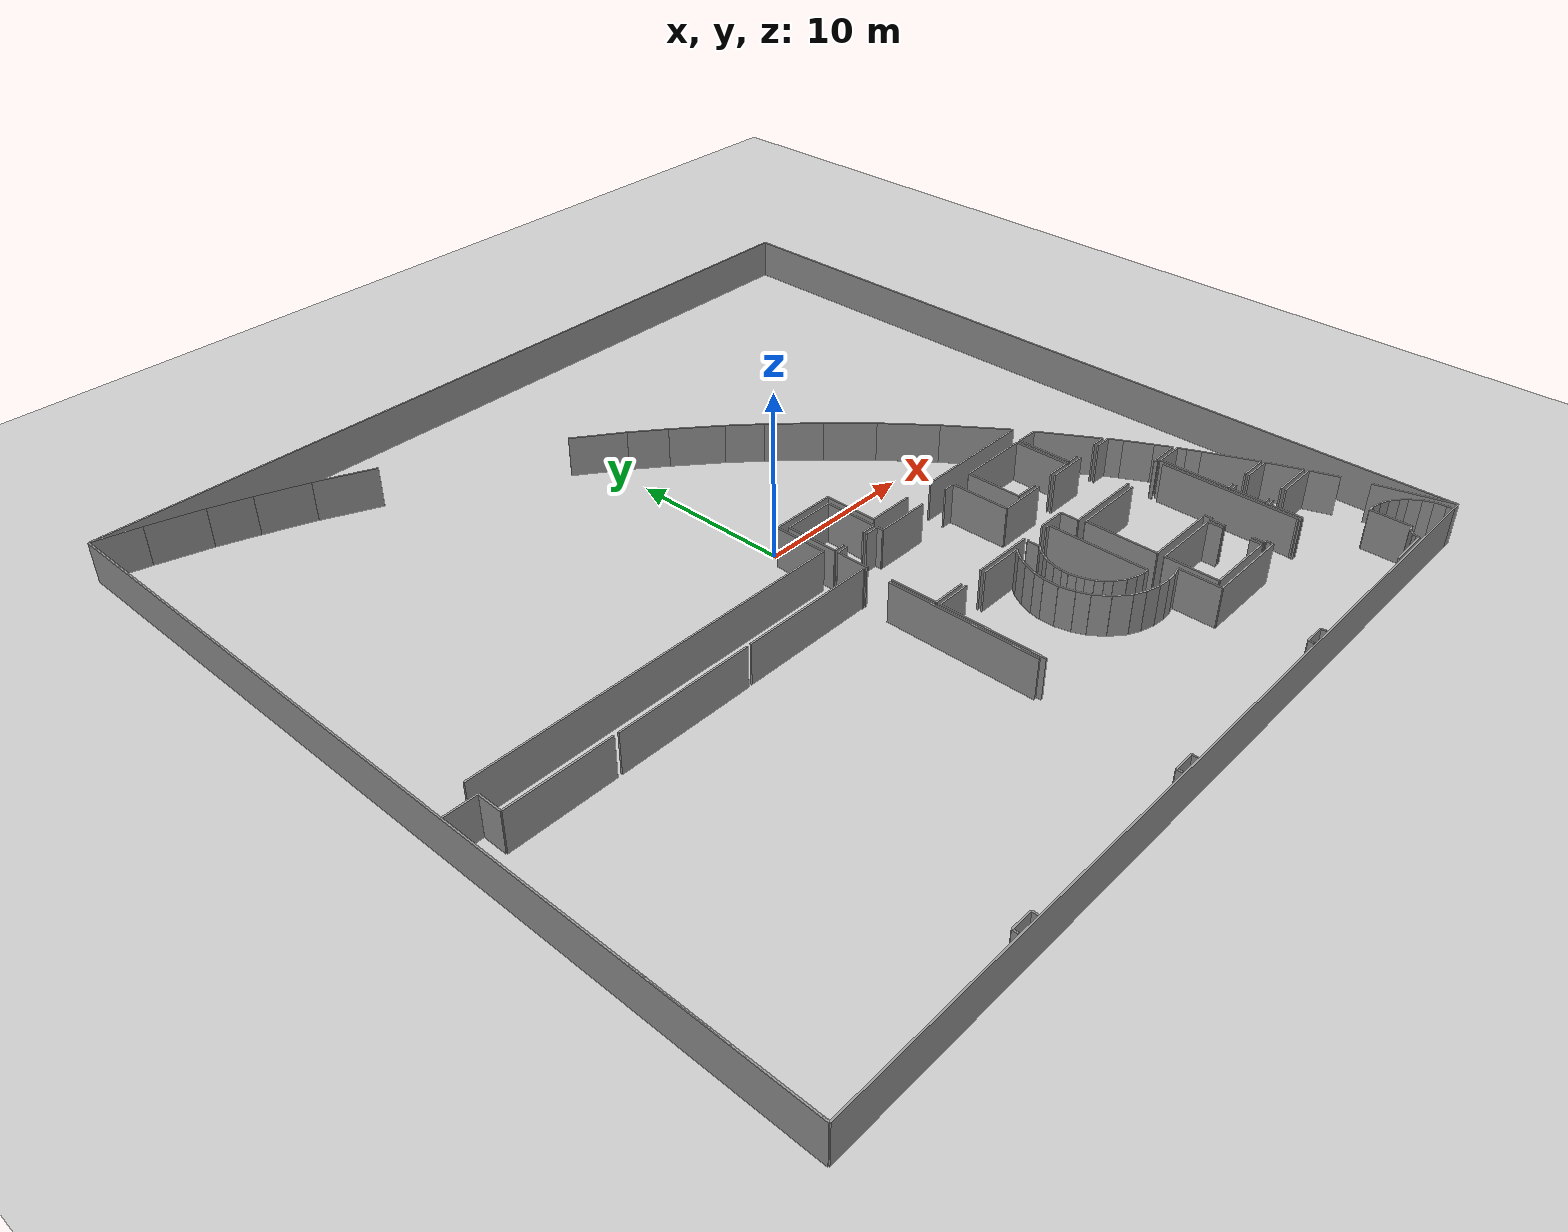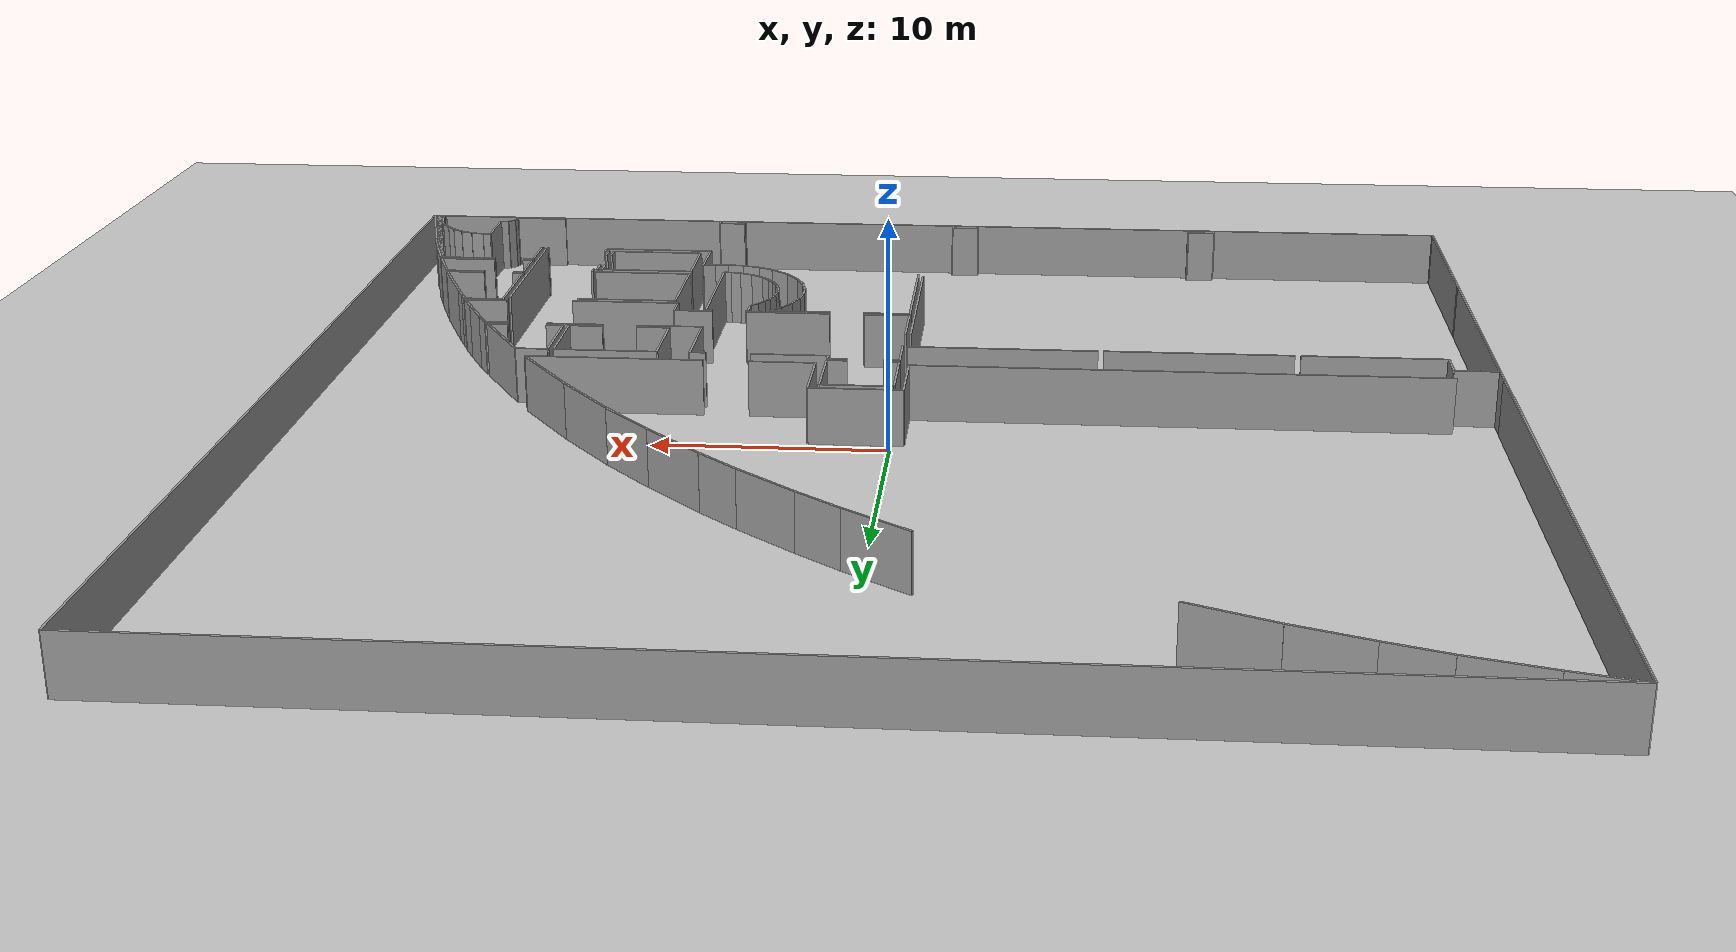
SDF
<sdf version="1.6">
  <world name="default">
    <light name="sun" type="directional">
      <cast_shadows>1</cast_shadows>
      <pose frame="">0 0 10 0 -0 0</pose>
      <diffuse>0.8 0.8 0.8 1</diffuse>
      <specular>0.1 0.1 0.1 1</specular>
      <attenuation>
        <range>1000</range>
        <constant>0.9</constant>
        <linear>0.01</linear>
        <quadratic>0.001</quadratic>
      </attenuation>
      <direction>-0.5 0.5 -1</direction>
    </light>
    <model name="ground_plane">
      <static>1</static>
      <link name="link">
        <collision name="collision">
          <geometry>
            <plane>
              <normal>0 0 1</normal>
              <size>100 100</size>
            </plane>
          </geometry>
          <surface>
            <friction>
              <ode>
                <mu>100</mu>
                <mu2>50</mu2>
              </ode>
              <torsional>
                <ode />
              </torsional>
            </friction>
            <contact>
              <ode />
            </contact>
            <bounce />
          </surface>
          <max_contacts>10</max_contacts>
        </collision>
        <visual name="visual">
          <cast_shadows>0</cast_shadows>
          <geometry>
            <plane>
              <normal>0 0 1</normal>
              <size>100 100</size>
            </plane>
          </geometry>
          <material>
            <script>
              <uri>file://media/materials/scripts/gazebo.material</uri>
              <name>Gazebo/Grey</name>
            </script>
          </material>
        </visual>
        <self_collide>0</self_collide>
        <kinematic>0</kinematic>
        <gravity>1</gravity>
      </link>
    </model>
    <gravity>0 0 -9.8</gravity>
    <magnetic_field>6e-06 2.3e-05 -4.2e-05</magnetic_field>
    <atmosphere type="adiabatic" />
    <physics default="0" name="default_physics" type="ode">
      <max_step_size>0.001</max_step_size>
      <real_time_factor>1</real_time_factor>
      <real_time_update_rate>1000</real_time_update_rate>
    </physics>
    <scene>
      <ambient>0.4 0.4 0.4 1</ambient>
      <background>0.7 0.7 0.7 1</background>
      <shadows>1</shadows>
    </scene>
    <spherical_coordinates>
      <surface_model>EARTH_WGS84</surface_model>
      <latitude_deg>0</latitude_deg>
      <longitude_deg>0</longitude_deg>
      <elevation>0</elevation>
      <heading_deg>0</heading_deg>
    </spherical_coordinates>
  <model name="50041194">
		<static>1</static>
		<link name="Wall_0">
			<collision name="Wall_0_Collision">
				<geometry>
					<box>
						<size>28.5608519399 0.1 2.5</size>
					</box>
				</geometry>
				<pose frame="">14.2804259699 0 1.25 0 0 0</pose>
			</collision>
			<visual name="Wall_0_Visual">
				<pose frame="">14.2804259699 0 1.25 0 0 0</pose>
				<geometry>
					<box>
						<size>28.5608519399 0.1 2.5</size>
					</box>
				</geometry>
				<material>
					<script>
						<uri>file://media/materials/scripts/gazebo.material</uri>
						<name>Gazebo/Grey</name>
					</script>
					<ambient>1 1 1 1</ambient>
				</material>
			</visual>
			<pose frame="">0.00902263282967 -28.5608519399 0 0 0 1.57079632679</pose>
		</link>
		<link name="Wall_1">
			<collision name="Wall_1_Collision">
				<geometry>
					<box>
						<size>2.74540686243 0.1 2.5</size>
					</box>
				</geometry>
				<pose frame="">1.37270343121 0 1.25 0 0 0</pose>
			</collision>
			<visual name="Wall_1_Visual">
				<pose frame="">1.37270343121 0 1.25 0 0 0</pose>
				<geometry>
					<box>
						<size>2.74540686243 0.1 2.5</size>
					</box>
				</geometry>
				<material>
					<script>
						<uri>file://media/materials/scripts/gazebo.material</uri>
						<name>Gazebo/Grey</name>
					</script>
					<ambient>1 1 1 1</ambient>
				</material>
			</visual>
			<pose frame="">0.00902263282967 -0.0 0 0 0 -0.241682561469</pose>
		</link>
		<link name="Wall_2">
			<collision name="Wall_2_Collision">
				<geometry>
					<box>
						<size>3.28572289443 0.1 2.5</size>
					</box>
				</geometry>
				<pose frame="">1.64286144721 0 1.25 0 0 0</pose>
			</collision>
			<visual name="Wall_2_Visual">
				<pose frame="">1.64286144721 0 1.25 0 0 0</pose>
				<geometry>
					<box>
						<size>3.28572289443 0.1 2.5</size>
					</box>
				</geometry>
				<material>
					<script>
						<uri>file://media/materials/scripts/gazebo.material</uri>
						<name>Gazebo/Grey</name>
					</script>
					<ambient>1 1 1 1</ambient>
				</material>
			</visual>
			<pose frame="">2.67463877699 -0.657076412805 0 0 0 -0.278561038296</pose>
		</link>
		<link name="Wall_3">
			<collision name="Wall_3_Collision">
				<geometry>
					<box>
						<size>2.48383758283 0.1 2.5</size>
					</box>
				</geometry>
				<pose frame="">1.24191879142 0 1.25 0 0 0</pose>
			</collision>
			<visual name="Wall_3_Visual">
				<pose frame="">1.24191879142 0 1.25 0 0 0</pose>
				<geometry>
					<box>
						<size>2.48383758283 0.1 2.5</size>
					</box>
				</geometry>
				<material>
					<script>
						<uri>file://media/materials/scripts/gazebo.material</uri>
						<name>Gazebo/Grey</name>
					</script>
					<ambient>1 1 1 1</ambient>
				</material>
			</visual>
			<pose frame="">5.8337039814 -1.56055965739 0 0 0 -0.337022508484</pose>
		</link>
		<link name="Wall_4">
			<collision name="Wall_4_Collision">
				<geometry>
					<box>
						<size>3.13700223776 0.1 2.5</size>
					</box>
				</geometry>
				<pose frame="">1.56850111888 0 1.25 0 0 0</pose>
			</collision>
			<visual name="Wall_4_Visual">
				<pose frame="">1.56850111888 0 1.25 0 0 0</pose>
				<geometry>
					<box>
						<size>3.13700223776 0.1 2.5</size>
					</box>
				</geometry>
				<material>
					<script>
						<uri>file://media/materials/scripts/gazebo.material</uri>
						<name>Gazebo/Grey</name>
					</script>
					<ambient>1 1 1 1</ambient>
				</material>
			</visual>
			<pose frame="">8.17780940641 -2.38191152737 0 0 0 -0.361717875042</pose>
		</link>
		<link name="Wall_5">
			<collision name="Wall_5_Collision">
				<geometry>
					<box>
						<size>3.66875521495 0.1 2.5</size>
					</box>
				</geometry>
				<pose frame="">1.83437760747 0 1.25 0 0 0</pose>
			</collision>
			<visual name="Wall_5_Visual">
				<pose frame="">1.83437760747 0 1.25 0 0 0</pose>
				<geometry>
					<box>
						<size>3.66875521495 0.1 2.5</size>
					</box>
				</geometry>
				<material>
					<script>
						<uri>file://media/materials/scripts/gazebo.material</uri>
						<name>Gazebo/Grey</name>
					</script>
					<ambient>1 1 1 1</ambient>
				</material>
			</visual>
			<pose frame="">11.1118171074 -3.49203847962 0 0 0 -0.420229011525</pose>
		</link>
		<link name="Wall_6">
			<collision name="Wall_6_Collision">
				<geometry>
					<box>
						<size>3.37259636429 0.1 2.5</size>
					</box>
				</geometry>
				<pose frame="">1.68629818215 0 1.25 0 0 0</pose>
			</collision>
			<visual name="Wall_6_Visual">
				<pose frame="">1.68629818215 0 1.25 0 0 0</pose>
				<geometry>
					<box>
						<size>3.37259636429 0.1 2.5</size>
					</box>
				</geometry>
				<material>
					<script>
						<uri>file://media/materials/scripts/gazebo.material</uri>
						<name>Gazebo/Grey</name>
					</script>
					<ambient>1 1 1 1</ambient>
				</material>
			</visual>
			<pose frame="">23.7077937757 -10.3464436848 0 0 0 -0.625089634434</pose>
		</link>
		<link name="Wall_7">
			<collision name="Wall_7_Collision">
				<geometry>
					<box>
						<size>2.4044219948 0.1 2.5</size>
					</box>
				</geometry>
				<pose frame="">1.2022109974 0 1.25 0 0 0</pose>
			</collision>
			<visual name="Wall_7_Visual">
				<pose frame="">1.2022109974 0 1.25 0 0 0</pose>
				<geometry>
					<box>
						<size>2.4044219948 0.1 2.5</size>
					</box>
				</geometry>
				<material>
					<script>
						<uri>file://media/materials/scripts/gazebo.material</uri>
						<name>Gazebo/Grey</name>
					</script>
					<ambient>1 1 1 1</ambient>
				</material>
			</visual>
			<pose frame="">26.4426681577 -12.3199857671 0 0 0 -0.679173434862</pose>
		</link>
		<link name="Wall_8">
			<collision name="Wall_8_Collision">
				<geometry>
					<box>
						<size>3.28038153814 0.1 2.5</size>
					</box>
				</geometry>
				<pose frame="">1.64019076907 0 1.25 0 0 0</pose>
			</collision>
			<visual name="Wall_8_Visual">
				<pose frame="">1.64019076907 0 1.25 0 0 0</pose>
				<geometry>
					<box>
						<size>3.28038153814 0.1 2.5</size>
					</box>
				</geometry>
				<material>
					<script>
						<uri>file://media/materials/scripts/gazebo.material</uri>
						<name>Gazebo/Grey</name>
					</script>
					<ambient>1 1 1 1</ambient>
				</material>
			</visual>
			<pose frame="">28.3135301369 -13.8303236711 0 0 0 -0.709529671184</pose>
		</link>
		<link name="Wall_9">
			<collision name="Wall_9_Collision">
				<geometry>
					<box>
						<size>2.27547560029 0.1 2.5</size>
					</box>
				</geometry>
				<pose frame="">1.13773780015 0 1.25 0 0 0</pose>
			</collision>
			<visual name="Wall_9_Visual">
				<pose frame="">1.13773780015 0 1.25 0 0 0</pose>
				<geometry>
					<box>
						<size>2.27547560029 0.1 2.5</size>
					</box>
				</geometry>
				<material>
					<script>
						<uri>file://media/materials/scripts/gazebo.material</uri>
						<name>Gazebo/Grey</name>
					</script>
					<ambient>1 1 1 1</ambient>
				</material>
			</visual>
			<pose frame="">30.8022518458 -15.9674168583 0 0 0 -0.753563801183</pose>
		</link>
		<link name="Wall_10">
			<collision name="Wall_10_Collision">
				<geometry>
					<box>
						<size>3.47212504948 0.1 2.5</size>
					</box>
				</geometry>
				<pose frame="">1.73606252474 0 1.25 0 0 0</pose>
			</collision>
			<visual name="Wall_10_Visual">
				<pose frame="">1.73606252474 0 1.25 0 0 0</pose>
				<geometry>
					<box>
						<size>3.47212504948 0.1 2.5</size>
					</box>
				</geometry>
				<material>
					<script>
						<uri>file://media/materials/scripts/gazebo.material</uri>
						<name>Gazebo/Grey</name>
					</script>
					<ambient>1 1 1 1</ambient>
				</material>
			</visual>
			<pose frame="">32.4616538105 -17.5243928785 0 0 0 -0.795180966372</pose>
		</link>
		<link name="Wall_11">
			<collision name="Wall_11_Collision">
				<geometry>
					<box>
						<size>3.1130207171 0.1 2.5</size>
					</box>
				</geometry>
				<pose frame="">1.55651035855 0 1.25 0 0 0</pose>
			</collision>
			<visual name="Wall_11_Visual">
				<pose frame="">1.55651035855 0 1.25 0 0 0</pose>
				<geometry>
					<box>
						<size>3.1130207171 0.1 2.5</size>
					</box>
				</geometry>
				<material>
					<script>
						<uri>file://media/materials/scripts/gazebo.material</uri>
						<name>Gazebo/Grey</name>
					</script>
					<ambient>1 1 1 1</ambient>
				</material>
			</visual>
			<pose frame="">34.8926815011 -20.0034565579 0 0 0 -0.837783997723</pose>
		</link>
		<link name="Wall_12">
			<collision name="Wall_12_Collision">
				<geometry>
					<box>
						<size>3.6700077052 0.1 2.5</size>
					</box>
				</geometry>
				<pose frame="">1.8350038526 0 1.25 0 0 0</pose>
			</collision>
			<visual name="Wall_12_Visual">
				<pose frame="">1.8350038526 0 1.25 0 0 0</pose>
				<geometry>
					<box>
						<size>3.6700077052 0.1 2.5</size>
					</box>
				</geometry>
				<material>
					<script>
						<uri>file://media/materials/scripts/gazebo.material</uri>
						<name>Gazebo/Grey</name>
					</script>
					<ambient>1 1 1 1</ambient>
				</material>
			</visual>
			<pose frame="">36.9756388914 -22.3169358631 0 0 0 -0.895433494104</pose>
		</link>
		<link name="Wall_13">
			<collision name="Wall_13_Collision">
				<geometry>
					<box>
						<size>4.07445456339 0.1 2.5</size>
					</box>
				</geometry>
				<pose frame="">2.0372272817 0 1.25 0 0 0</pose>
			</collision>
			<visual name="Wall_13_Visual">
				<pose frame="">2.0372272817 0 1.25 0 0 0</pose>
				<geometry>
					<box>
						<size>4.07445456339 0.1 2.5</size>
					</box>
				</geometry>
				<material>
					<script>
						<uri>file://media/materials/scripts/gazebo.material</uri>
						<name>Gazebo/Grey</name>
					</script>
					<ambient>1 1 1 1</ambient>
				</material>
			</visual>
			<pose frame="">39.2700562961 -25.1813040881 0 0 0 -0.949198087053</pose>
		</link>
		<link name="Wall_14">
			<collision name="Wall_14_Collision">
				<geometry>
					<box>
						<size>0.130030728321 0.1 2.5</size>
					</box>
				</geometry>
				<pose frame="">0.0650153641607 0 1.25 0 0 0</pose>
			</collision>
			<visual name="Wall_14_Visual">
				<pose frame="">0.0650153641607 0 1.25 0 0 0</pose>
				<geometry>
					<box>
						<size>0.130030728321 0.1 2.5</size>
					</box>
				</geometry>
				<material>
					<script>
						<uri>file://media/materials/scripts/gazebo.material</uri>
						<name>Gazebo/Grey</name>
					</script>
					<ambient>1 1 1 1</ambient>
				</material>
			</visual>
			<pose frame="">41.6427545717 -28.4936269713 0 0 0 -1.10671165488</pose>
		</link>
		<link name="Wall_15">
			<collision name="Wall_15_Collision">
				<geometry>
					<box>
						<size>7.74739169664 0.1 2.5</size>
					</box>
				</geometry>
				<pose frame="">3.87369584832 0 1.25 0 0 0</pose>
			</collision>
			<visual name="Wall_15_Visual">
				<pose frame="">3.87369584832 0 1.25 0 0 0</pose>
				<geometry>
					<box>
						<size>7.74739169664 0.1 2.5</size>
					</box>
				</geometry>
				<material>
					<script>
						<uri>file://media/materials/scripts/gazebo.material</uri>
						<name>Gazebo/Grey</name>
					</script>
					<ambient>1 1 1 1</ambient>
				</material>
			</visual>
			<pose frame="">41.7009569074 -28.6099045634 0 0 0 3.14159265359</pose>
		</link>
		<link name="Wall_16">
			<collision name="Wall_16_Collision">
				<geometry>
					<box>
						<size>2.90630440584 0.1 2.5</size>
					</box>
				</geometry>
				<pose frame="">1.45315220292 0 1.25 0 0 0</pose>
			</collision>
			<visual name="Wall_16_Visual">
				<pose frame="">1.45315220292 0 1.25 0 0 0</pose>
				<geometry>
					<box>
						<size>2.90630440584 0.1 2.5</size>
					</box>
				</geometry>
				<material>
					<script>
						<uri>file://media/materials/scripts/gazebo.material</uri>
						<name>Gazebo/Grey</name>
					</script>
					<ambient>1 1 1 1</ambient>
				</material>
			</visual>
			<pose frame="">31.9997204255 -28.6099045634 0 0 0 3.14159265359</pose>
		</link>
		<link name="Wall_17">
			<collision name="Wall_17_Collision">
				<geometry>
					<box>
						<size>3.21332808072 0.1 2.5</size>
					</box>
				</geometry>
				<pose frame="">1.60666404036 0 1.25 0 0 0</pose>
			</collision>
			<visual name="Wall_17_Visual">
				<pose frame="">1.60666404036 0 1.25 0 0 0</pose>
				<geometry>
					<box>
						<size>3.21332808072 0.1 2.5</size>
					</box>
				</geometry>
				<material>
					<script>
						<uri>file://media/materials/scripts/gazebo.material</uri>
						<name>Gazebo/Grey</name>
					</script>
					<ambient>1 1 1 1</ambient>
				</material>
			</visual>
			<pose frame="">29.0934160196 -28.6099045634 0 0 0 1.57079632679</pose>
		</link>
		<link name="Wall_18">
			<collision name="Wall_18_Collision">
				<geometry>
					<box>
						<size>4.01227586382 0.1 2.5</size>
					</box>
				</geometry>
				<pose frame="">2.00613793191 0 1.25 0 0 0</pose>
			</collision>
			<visual name="Wall_18_Visual">
				<pose frame="">2.00613793191 0 1.25 0 0 0</pose>
				<geometry>
					<box>
						<size>4.01227586382 0.1 2.5</size>
					</box>
				</geometry>
				<material>
					<script>
						<uri>file://media/materials/scripts/gazebo.material</uri>
						<name>Gazebo/Grey</name>
					</script>
					<ambient>1 1 1 1</ambient>
				</material>
			</visual>
			<pose frame="">29.0934160196 -25.3965764827 0 0 0 3.14159265359</pose>
		</link>
		<link name="Wall_19">
			<collision name="Wall_19_Collision">
				<geometry>
					<box>
						<size>3.21231144604 0.1 2.5</size>
					</box>
				</geometry>
				<pose frame="">1.60615572302 0 1.25 0 0 0</pose>
			</collision>
			<visual name="Wall_19_Visual">
				<pose frame="">1.60615572302 0 1.25 0 0 0</pose>
				<geometry>
					<box>
						<size>3.21231144604 0.1 2.5</size>
					</box>
				</geometry>
				<material>
					<script>
						<uri>file://media/materials/scripts/gazebo.material</uri>
						<name>Gazebo/Grey</name>
					</script>
					<ambient>1 1 1 1</ambient>
				</material>
			</visual>
			<pose frame="">25.0811401558 -25.3965764827 0 0 0 -1.57079632679</pose>
		</link>
		<link name="Wall_20">
			<collision name="Wall_20_Collision">
				<geometry>
					<box>
						<size>23.117256103 0.1 2.5</size>
					</box>
				</geometry>
				<pose frame="">11.5586280515 0 1.25 0 0 0</pose>
			</collision>
			<visual name="Wall_20_Visual">
				<pose frame="">11.5586280515 0 1.25 0 0 0</pose>
				<geometry>
					<box>
						<size>23.117256103 0.1 2.5</size>
					</box>
				</geometry>
				<material>
					<script>
						<uri>file://media/materials/scripts/gazebo.material</uri>
						<name>Gazebo/Grey</name>
					</script>
					<ambient>1 1 1 1</ambient>
				</material>
			</visual>
			<pose frame="">25.0811401558 -28.6088879287 0 0 0 3.14159265359</pose>
		</link>
		<link name="Wall_21">
			<collision name="Wall_21_Collision">
				<geometry>
					<box>
						<size>0.0488760077102 0.1 2.5</size>
					</box>
				</geometry>
				<pose frame="">0.0244380038551 0 1.25 0 0 0</pose>
			</collision>
			<visual name="Wall_21_Visual">
				<pose frame="">0.0244380038551 0 1.25 0 0 0</pose>
				<geometry>
					<box>
						<size>0.0488760077102 0.1 2.5</size>
					</box>
				</geometry>
				<material>
					<script>
						<uri>file://media/materials/scripts/gazebo.material</uri>
						<name>Gazebo/Grey</name>
					</script>
					<ambient>1 1 1 1</ambient>
				</material>
			</visual>
			<pose frame="">0.0 -28.6088879287 0 0 0 1.38512893902</pose>
		</link>
		<link name="Wall_22">
			<collision name="Wall_22_Collision">
				<geometry>
					<box>
						<size>12.1464970581 0.1 2.5</size>
					</box>
				</geometry>
				<pose frame="">6.07324852906 0 1.25 0 0 0</pose>
			</collision>
			<visual name="Wall_22_Visual">
				<pose frame="">6.07324852906 0 1.25 0 0 0</pose>
				<geometry>
					<box>
						<size>12.1464970581 0.1 2.5</size>
					</box>
				</geometry>
				<material>
					<script>
						<uri>file://media/materials/scripts/gazebo.material</uri>
						<name>Gazebo/Grey</name>
					</script>
					<ambient>1 1 1 1</ambient>
				</material>
			</visual>
			<pose frame="">0.00419361807576 -41.7663011018 0 0 0 1.57079632679</pose>
		</link>
		<link name="Wall_23">
			<collision name="Wall_23_Collision">
				<geometry>
					<box>
						<size>1.93999313772 0.1 2.5</size>
					</box>
				</geometry>
				<pose frame="">0.969996568858 0 1.25 0 0 0</pose>
			</collision>
			<visual name="Wall_23_Visual">
				<pose frame="">0.969996568858 0 1.25 0 0 0</pose>
				<geometry>
					<box>
						<size>1.93999313772 0.1 2.5</size>
					</box>
				</geometry>
				<material>
					<script>
						<uri>file://media/materials/scripts/gazebo.material</uri>
						<name>Gazebo/Grey</name>
					</script>
					<ambient>1 1 1 1</ambient>
				</material>
			</visual>
			<pose frame="">0.00419361807576 -29.6198040437 0 0 0 0.0</pose>
		</link>
		<link name="Wall_24">
			<collision name="Wall_24_Collision">
				<geometry>
					<box>
						<size>1.49521546301 0.1 2.5</size>
					</box>
				</geometry>
				<pose frame="">0.747607731507 0 1.25 0 0 0</pose>
			</collision>
			<visual name="Wall_24_Visual">
				<pose frame="">0.747607731507 0 1.25 0 0 0</pose>
				<geometry>
					<box>
						<size>1.49521546301 0.1 2.5</size>
					</box>
				</geometry>
				<material>
					<script>
						<uri>file://media/materials/scripts/gazebo.material</uri>
						<name>Gazebo/Grey</name>
					</script>
					<ambient>1 1 1 1</ambient>
				</material>
			</visual>
			<pose frame="">1.94418675579 -29.6198040437 0 0 0 -1.57079632679</pose>
		</link>
		<link name="Wall_25">
			<collision name="Wall_25_Collision">
				<geometry>
					<box>
						<size>6.31444510808 0.1 2.5</size>
					</box>
				</geometry>
				<pose frame="">3.15722255404 0 1.25 0 0 0</pose>
			</collision>
			<visual name="Wall_25_Visual">
				<pose frame="">3.15722255404 0 1.25 0 0 0</pose>
				<geometry>
					<box>
						<size>6.31444510808 0.1 2.5</size>
					</box>
				</geometry>
				<material>
					<script>
						<uri>file://media/materials/scripts/gazebo.material</uri>
						<name>Gazebo/Grey</name>
					</script>
					<ambient>1 1 1 1</ambient>
				</material>
			</visual>
			<pose frame="">1.94418675579 -31.1150195067 0 0 0 0.0</pose>
		</link>
		<link name="Wall_26">
			<collision name="Wall_26_Collision">
				<geometry>
					<box>
						<size>0.0650725618159 0.1 2.5</size>
					</box>
				</geometry>
				<pose frame="">0.032536280908 0 1.25 0 0 0</pose>
			</collision>
			<visual name="Wall_26_Visual">
				<pose frame="">0.032536280908 0 1.25 0 0 0</pose>
				<geometry>
					<box>
						<size>0.0650725618159 0.1 2.5</size>
					</box>
				</geometry>
				<material>
					<script>
						<uri>file://media/materials/scripts/gazebo.material</uri>
						<name>Gazebo/Grey</name>
					</script>
					<ambient>1 1 1 1</ambient>
				</material>
			</visual>
			<pose frame="">0.00521025276079 -41.8313657216 0 0 0 1.58642005542</pose>
		</link>
		<link name="Wall_27">
			<collision name="Wall_27_Collision">
				<geometry>
					<box>
						<size>8.25138834174 0.1 2.5</size>
					</box>
				</geometry>
				<pose frame="">4.12569417087 0 1.25 0 0 0</pose>
			</collision>
			<visual name="Wall_27_Visual">
				<pose frame="">4.12569417087 0 1.25 0 0 0</pose>
				<geometry>
					<box>
						<size>8.25138834174 0.1 2.5</size>
					</box>
				</geometry>
				<material>
					<script>
						<uri>file://media/materials/scripts/gazebo.material</uri>
						<name>Gazebo/Grey</name>
					</script>
					<ambient>1 1 1 1</ambient>
				</material>
			</visual>
			<pose frame="">8.5126634558 -31.1228984255 0 0 0 0.0</pose>
		</link>
		<link name="Wall_28">
			<collision name="Wall_28_Collision">
				<geometry>
					<box>
						<size>8.28862258708 0.1 2.5</size>
					</box>
				</geometry>
				<pose frame="">4.14431129354 0 1.25 0 0 0</pose>
			</collision>
			<visual name="Wall_28_Visual">
				<pose frame="">4.14431129354 0 1.25 0 0 0</pose>
				<geometry>
					<box>
						<size>8.28862258708 0.1 2.5</size>
					</box>
				</geometry>
				<material>
					<script>
						<uri>file://media/materials/scripts/gazebo.material</uri>
						<name>Gazebo/Grey</name>
					</script>
					<ambient>1 1 1 1</ambient>
				</material>
			</visual>
			<pose frame="">16.9969882197 -31.1028198905 0 0 0 0.0</pose>
		</link>
		<link name="Wall_29">
			<collision name="Wall_29_Collision">
				<geometry>
					<box>
						<size>0.112973529374 0.1 2.5</size>
					</box>
				</geometry>
				<pose frame="">0.0564867646872 0 1.25 0 0 0</pose>
			</collision>
			<visual name="Wall_29_Visual">
				<pose frame="">0.0564867646872 0 1.25 0 0 0</pose>
				<geometry>
					<box>
						<size>0.112973529374 0.1 2.5</size>
					</box>
				</geometry>
				<material>
					<script>
						<uri>file://media/materials/scripts/gazebo.material</uri>
						<name>Gazebo/Grey</name>
					</script>
					<ambient>1 1 1 1</ambient>
				</material>
			</visual>
			<pose frame="">25.2856108068 -31.1028198905 0 0 0 -1.57079632679</pose>
		</link>
		<link name="Wall_30">
			<collision name="Wall_30_Collision">
				<geometry>
					<box>
						<size>9.06164618571 0.1 2.5</size>
					</box>
				</geometry>
				<pose frame="">4.53082309286 0 1.25 0 0 0</pose>
			</collision>
			<visual name="Wall_30_Visual">
				<pose frame="">4.53082309286 0 1.25 0 0 0</pose>
				<geometry>
					<box>
						<size>9.06164618571 0.1 2.5</size>
					</box>
				</geometry>
				<material>
					<script>
						<uri>file://media/materials/scripts/gazebo.material</uri>
						<name>Gazebo/Grey</name>
					</script>
					<ambient>1 1 1 1</ambient>
				</material>
			</visual>
			<pose frame="">25.2856108068 -32.793229213 0 0 0 -1.57079632679</pose>
		</link>
		<link name="Wall_31">
			<collision name="Wall_31_Collision">
				<geometry>
					<box>
						<size>2.8155697602 0.1 2.5</size>
					</box>
				</geometry>
				<pose frame="">1.4077848801 0 1.25 0 0 0</pose>
			</collision>
			<visual name="Wall_31_Visual">
				<pose frame="">1.4077848801 0 1.25 0 0 0</pose>
				<geometry>
					<box>
						<size>2.8155697602 0.1 2.5</size>
					</box>
				</geometry>
				<material>
					<script>
						<uri>file://media/materials/scripts/gazebo.material</uri>
						<name>Gazebo/Grey</name>
					</script>
					<ambient>1 1 1 1</ambient>
				</material>
			</visual>
			<pose frame="">25.515116087 -35.5713105692 0 0 0 1.57079632679</pose>
		</link>
		<link name="Wall_32">
			<collision name="Wall_32_Collision">
				<geometry>
					<box>
						<size>1.9688401469 0.1 2.5</size>
					</box>
				</geometry>
				<pose frame="">0.984420073452 0 1.25 0 0 0</pose>
			</collision>
			<visual name="Wall_32_Visual">
				<pose frame="">0.984420073452 0 1.25 0 0 0</pose>
				<geometry>
					<box>
						<size>1.9688401469 0.1 2.5</size>
					</box>
				</geometry>
				<material>
					<script>
						<uri>file://media/materials/scripts/gazebo.material</uri>
						<name>Gazebo/Grey</name>
					</script>
					<ambient>1 1 1 1</ambient>
				</material>
			</visual>
			<pose frame="">25.515116087 -31.1894879974 0 0 0 1.57079632679</pose>
		</link>
		<link name="Wall_33">
			<collision name="Wall_33_Collision">
				<geometry>
					<box>
						<size>0.689913713131 0.1 2.5</size>
					</box>
				</geometry>
				<pose frame="">0.344956856566 0 1.25 0 0 0</pose>
			</collision>
			<visual name="Wall_33_Visual">
				<pose frame="">0.344956856566 0 1.25 0 0 0</pose>
				<geometry>
					<box>
						<size>0.689913713131 0.1 2.5</size>
					</box>
				</geometry>
				<material>
					<script>
						<uri>file://media/materials/scripts/gazebo.material</uri>
						<name>Gazebo/Grey</name>
					</script>
					<ambient>1 1 1 1</ambient>
				</material>
			</visual>
			<pose frame="">25.515116087 -29.2206478505 0 0 0 0.0</pose>
		</link>
		<link name="Wall_34">
			<collision name="Wall_34_Collision">
				<geometry>
					<box>
						<size>0.870112211053 0.1 2.5</size>
					</box>
				</geometry>
				<pose frame="">0.435056105527 0 1.25 0 0 0</pose>
			</collision>
			<visual name="Wall_34_Visual">
				<pose frame="">0.435056105527 0 1.25 0 0 0</pose>
				<geometry>
					<box>
						<size>0.870112211053 0.1 2.5</size>
					</box>
				</geometry>
				<material>
					<script>
						<uri>file://media/materials/scripts/gazebo.material</uri>
						<name>Gazebo/Grey</name>
					</script>
					<ambient>1 1 1 1</ambient>
				</material>
			</visual>
			<pose frame="">27.7640390896 -29.2206478505 0 0 0 0.0</pose>
		</link>
		<link name="Wall_35">
			<collision name="Wall_35_Collision">
				<geometry>
					<box>
						<size>0.395470892478 0.1 2.5</size>
					</box>
				</geometry>
				<pose frame="">0.197735446239 0 1.25 0 0 0</pose>
			</collision>
			<visual name="Wall_35_Visual">
				<pose frame="">0.197735446239 0 1.25 0 0 0</pose>
				<geometry>
					<box>
						<size>0.395470892478 0.1 2.5</size>
					</box>
				</geometry>
				<material>
					<script>
						<uri>file://media/materials/scripts/gazebo.material</uri>
						<name>Gazebo/Grey</name>
					</script>
					<ambient>1 1 1 1</ambient>
				</material>
			</visual>
			<pose frame="">28.6341513007 -29.2206478505 0 0 0 -1.57079632679</pose>
		</link>
		<link name="Wall_36">
			<collision name="Wall_36_Collision">
				<geometry>
					<box>
						<size>3.37357512295 0.1 2.5</size>
					</box>
				</geometry>
				<pose frame="">1.68678756147 0 1.25 0 0 0</pose>
			</collision>
			<visual name="Wall_36_Visual">
				<pose frame="">1.68678756147 0 1.25 0 0 0</pose>
				<geometry>
					<box>
						<size>3.37357512295 0.1 2.5</size>
					</box>
				</geometry>
				<material>
					<script>
						<uri>file://media/materials/scripts/gazebo.material</uri>
						<name>Gazebo/Grey</name>
					</script>
					<ambient>1 1 1 1</ambient>
				</material>
			</visual>
			<pose frame="">28.6341513007 -29.6161187429 0 0 0 0.0</pose>
		</link>
		<link name="Wall_37">
			<collision name="Wall_37_Collision">
				<geometry>
					<box>
						<size>0.702113329352 0.1 2.5</size>
					</box>
				</geometry>
				<pose frame="">0.351056664676 0 1.25 0 0 0</pose>
			</collision>
			<visual name="Wall_37_Visual">
				<pose frame="">0.351056664676 0 1.25 0 0 0</pose>
				<geometry>
					<box>
						<size>0.702113329352 0.1 2.5</size>
					</box>
				</geometry>
				<material>
					<script>
						<uri>file://media/materials/scripts/gazebo.material</uri>
						<name>Gazebo/Grey</name>
					</script>
					<ambient>1 1 1 1</ambient>
				</material>
			</visual>
			<pose frame="">33.9738979045 -29.6161187429 0 0 0 0.0</pose>
		</link>
		<link name="Wall_38">
			<collision name="Wall_38_Collision">
				<geometry>
					<box>
						<size>3.6105780839 0.1 2.5</size>
					</box>
				</geometry>
				<pose frame="">1.80528904195 0 1.25 0 0 0</pose>
			</collision>
			<visual name="Wall_38_Visual">
				<pose frame="">1.80528904195 0 1.25 0 0 0</pose>
				<geometry>
					<box>
						<size>3.6105780839 0.1 2.5</size>
					</box>
				</geometry>
				<material>
					<script>
						<uri>file://media/materials/scripts/gazebo.material</uri>
						<name>Gazebo/Grey</name>
					</script>
					<ambient>1 1 1 1</ambient>
				</material>
			</visual>
			<pose frame="">34.6760112338 -29.6161187429 0 0 0 -1.57079632679</pose>
		</link>
		<link name="Wall_39">
			<collision name="Wall_39_Collision">
				<geometry>
					<box>
						<size>2.95522995006 0.1 2.5</size>
					</box>
				</geometry>
				<pose frame="">1.47761497503 0 1.25 0 0 0</pose>
			</collision>
			<visual name="Wall_39_Visual">
				<pose frame="">1.47761497503 0 1.25 0 0 0</pose>
				<geometry>
					<box>
						<size>2.95522995006 0.1 2.5</size>
					</box>
				</geometry>
				<material>
					<script>
						<uri>file://media/materials/scripts/gazebo.material</uri>
						<name>Gazebo/Grey</name>
					</script>
					<ambient>1 1 1 1</ambient>
				</material>
			</visual>
			<pose frame="">34.6760112338 -33.2266968268 0 0 0 0.0</pose>
		</link>
		<link name="Wall_40">
			<collision name="Wall_40_Collision">
				<geometry>
					<box>
						<size>2.56115693027 0.1 2.5</size>
					</box>
				</geometry>
				<pose frame="">1.28057846514 0 1.25 0 0 0</pose>
			</collision>
			<visual name="Wall_40_Visual">
				<pose frame="">1.28057846514 0 1.25 0 0 0</pose>
				<geometry>
					<box>
						<size>2.56115693027 0.1 2.5</size>
					</box>
				</geometry>
				<material>
					<script>
						<uri>file://media/materials/scripts/gazebo.material</uri>
						<name>Gazebo/Grey</name>
					</script>
					<ambient>1 1 1 1</ambient>
				</material>
			</visual>
			<pose frame="">39.1662324789 -33.2266968268 0 0 0 0.0</pose>
		</link>
		<link name="Wall_41">
			<collision name="Wall_41_Collision">
				<geometry>
					<box>
						<size>1.06200200785 0.1 2.5</size>
					</box>
				</geometry>
				<pose frame="">0.531001003927 0 1.25 0 0 0</pose>
			</collision>
			<visual name="Wall_41_Visual">
				<pose frame="">0.531001003927 0 1.25 0 0 0</pose>
				<geometry>
					<box>
						<size>1.06200200785 0.1 2.5</size>
					</box>
				</geometry>
				<material>
					<script>
						<uri>file://media/materials/scripts/gazebo.material</uri>
						<name>Gazebo/Grey</name>
					</script>
					<ambient>1 1 1 1</ambient>
				</material>
			</visual>
			<pose frame="">43.4758739881 -33.2266968268 0 0 0 0.0</pose>
		</link>
		<link name="Wall_42">
			<collision name="Wall_42_Collision">
				<geometry>
					<box>
						<size>0.878517241441 0.1 2.5</size>
					</box>
				</geometry>
				<pose frame="">0.43925862072 0 1.25 0 0 0</pose>
			</collision>
			<visual name="Wall_42_Visual">
				<pose frame="">0.43925862072 0 1.25 0 0 0</pose>
				<geometry>
					<box>
						<size>0.878517241441 0.1 2.5</size>
					</box>
				</geometry>
				<material>
					<script>
						<uri>file://media/materials/scripts/gazebo.material</uri>
						<name>Gazebo/Grey</name>
					</script>
					<ambient>1 1 1 1</ambient>
				</material>
			</visual>
			<pose frame="">44.537875996 -33.2266968268 0 0 0 -1.05595627726</pose>
		</link>
		<link name="Wall_43">
			<collision name="Wall_43_Collision">
				<geometry>
					<box>
						<size>1.73027096718 0.1 2.5</size>
					</box>
				</geometry>
				<pose frame="">0.865135483592 0 1.25 0 0 0</pose>
			</collision>
			<visual name="Wall_43_Visual">
				<pose frame="">0.865135483592 0 1.25 0 0 0</pose>
				<geometry>
					<box>
						<size>1.73027096718 0.1 2.5</size>
					</box>
				</geometry>
				<material>
					<script>
						<uri>file://media/materials/scripts/gazebo.material</uri>
						<name>Gazebo/Grey</name>
					</script>
					<ambient>1 1 1 1</ambient>
				</material>
			</visual>
			<pose frame="">44.9704540545 -33.9913331893 0 0 0 -1.09414153496</pose>
		</link>
		<link name="Wall_44">
			<collision name="Wall_44_Collision">
				<geometry>
					<box>
						<size>1.04257971873 0.1 2.5</size>
					</box>
				</geometry>
				<pose frame="">0.521289859366 0 1.25 0 0 0</pose>
			</collision>
			<visual name="Wall_44_Visual">
				<pose frame="">0.521289859366 0 1.25 0 0 0</pose>
				<geometry>
					<box>
						<size>1.04257971873 0.1 2.5</size>
					</box>
				</geometry>
				<material>
					<script>
						<uri>file://media/materials/scripts/gazebo.material</uri>
						<name>Gazebo/Grey</name>
					</script>
					<ambient>1 1 1 1</ambient>
				</material>
			</visual>
			<pose frame="">45.7643186641 -35.5287389918 0 0 0 -1.09635541692</pose>
		</link>
		<link name="Wall_45">
			<collision name="Wall_45_Collision">
				<geometry>
					<box>
						<size>1.96350281481 0.1 2.5</size>
					</box>
				</geometry>
				<pose frame="">0.981751407404 0 1.25 0 0 0</pose>
			</collision>
			<visual name="Wall_45_Visual">
				<pose frame="">0.981751407404 0 1.25 0 0 0</pose>
				<geometry>
					<box>
						<size>1.96350281481 0.1 2.5</size>
					</box>
				</geometry>
				<material>
					<script>
						<uri>file://media/materials/scripts/gazebo.material</uri>
						<name>Gazebo/Grey</name>
					</script>
					<ambient>1 1 1 1</ambient>
				</material>
			</visual>
			<pose frame="">46.2406120141 -36.4561639832 0 0 0 3.14159265359</pose>
		</link>
		<link name="Wall_46">
			<collision name="Wall_46_Collision">
				<geometry>
					<box>
						<size>0.2140016012 0.1 2.5</size>
					</box>
				</geometry>
				<pose frame="">0.1070008006 0 1.25 0 0 0</pose>
			</collision>
			<visual name="Wall_46_Visual">
				<pose frame="">0.1070008006 0 1.25 0 0 0</pose>
				<geometry>
					<box>
						<size>0.2140016012 0.1 2.5</size>
					</box>
				</geometry>
				<material>
					<script>
						<uri>file://media/materials/scripts/gazebo.material</uri>
						<name>Gazebo/Grey</name>
					</script>
					<ambient>1 1 1 1</ambient>
				</material>
			</visual>
			<pose frame="">44.2771091993 -36.4561639832 0 0 0 -1.57079632679</pose>
		</link>
		<link name="Wall_47">
			<collision name="Wall_47_Collision">
				<geometry>
					<box>
						<size>4.93982793458 0.1 2.5</size>
					</box>
				</geometry>
				<pose frame="">2.46991396729 0 1.25 0 0 0</pose>
			</collision>
			<visual name="Wall_47_Visual">
				<pose frame="">2.46991396729 0 1.25 0 0 0</pose>
				<geometry>
					<box>
						<size>4.93982793458 0.1 2.5</size>
					</box>
				</geometry>
				<material>
					<script>
						<uri>file://media/materials/scripts/gazebo.material</uri>
						<name>Gazebo/Grey</name>
					</script>
					<ambient>1 1 1 1</ambient>
				</material>
			</visual>
			<pose frame="">41.2477919965 -36.6701655844 0 0 0 3.14159265359</pose>
		</link>
		<link name="Wall_48">
			<collision name="Wall_48_Collision">
				<geometry>
					<box>
						<size>1.10597145798 0.1 2.5</size>
					</box>
				</geometry>
				<pose frame="">0.552985728991 0 1.25 0 0 0</pose>
			</collision>
			<visual name="Wall_48_Visual">
				<pose frame="">0.552985728991 0 1.25 0 0 0</pose>
				<geometry>
					<box>
						<size>1.10597145798 0.1 2.5</size>
					</box>
				</geometry>
				<material>
					<script>
						<uri>file://media/materials/scripts/gazebo.material</uri>
						<name>Gazebo/Grey</name>
					</script>
					<ambient>1 1 1 1</ambient>
				</material>
			</visual>
			<pose frame="">36.307964062 -36.6701655844 0 0 0 1.57079632679</pose>
		</link>
		<link name="Wall_49">
			<collision name="Wall_49_Collision">
				<geometry>
					<box>
						<size>1.75216987966 0.1 2.5</size>
					</box>
				</geometry>
				<pose frame="">0.876084939828 0 1.25 0 0 0</pose>
			</collision>
			<visual name="Wall_49_Visual">
				<pose frame="">0.876084939828 0 1.25 0 0 0</pose>
				<geometry>
					<box>
						<size>1.75216987966 0.1 2.5</size>
					</box>
				</geometry>
				<material>
					<script>
						<uri>file://media/materials/scripts/gazebo.material</uri>
						<name>Gazebo/Grey</name>
					</script>
					<ambient>1 1 1 1</ambient>
				</material>
			</visual>
			<pose frame="">36.307964062 -35.5641941264 0 0 0 3.14159265359</pose>
		</link>
		<link name="Wall_50">
			<collision name="Wall_50_Collision">
				<geometry>
					<box>
						<size>3.8320773659 0.1 2.5</size>
					</box>
				</geometry>
				<pose frame="">1.91603868295 0 1.25 0 0 0</pose>
			</collision>
			<visual name="Wall_50_Visual">
				<pose frame="">1.91603868295 0 1.25 0 0 0</pose>
				<geometry>
					<box>
						<size>3.8320773659 0.1 2.5</size>
					</box>
				</geometry>
				<material>
					<script>
						<uri>file://media/materials/scripts/gazebo.material</uri>
						<name>Gazebo/Grey</name>
					</script>
					<ambient>1 1 1 1</ambient>
				</material>
			</visual>
			<pose frame="">32.9930995921 -35.5641941264 0 0 0 3.14159265359</pose>
		</link>
		<link name="Wall_51">
			<collision name="Wall_51_Collision">
				<geometry>
					<box>
						<size>2.06721180201 0.1 2.5</size>
					</box>
				</geometry>
				<pose frame="">1.033605901 0 1.25 0 0 0</pose>
			</collision>
			<visual name="Wall_51_Visual">
				<pose frame="">1.033605901 0 1.25 0 0 0</pose>
				<geometry>
					<box>
						<size>2.06721180201 0.1 2.5</size>
					</box>
				</geometry>
				<material>
					<script>
						<uri>file://media/materials/scripts/gazebo.material</uri>
						<name>Gazebo/Grey</name>
					</script>
					<ambient>1 1 1 1</ambient>
				</material>
			</visual>
			<pose frame="">27.5823156397 -35.5641941264 0 0 0 -3.13815011478</pose>
		</link>
		<link name="Wall_52">
			<collision name="Wall_52_Collision">
				<geometry>
					<box>
						<size>0.710754724174 0.1 2.5</size>
					</box>
				</geometry>
				<pose frame="">0.355377362087 0 1.25 0 0 0</pose>
			</collision>
			<visual name="Wall_52_Visual">
				<pose frame="">0.355377362087 0 1.25 0 0 0</pose>
				<geometry>
					<box>
						<size>0.710754724174 0.1 2.5</size>
					</box>
				</geometry>
				<material>
					<script>
						<uri>file://media/materials/scripts/gazebo.material</uri>
						<name>Gazebo/Grey</name>
					</script>
					<ambient>1 1 1 1</ambient>
				</material>
			</visual>
			<pose frame="">41.0639081979 -44.9492572213 0 0 0 1.57079632679</pose>
		</link>
		<link name="Wall_53">
			<collision name="Wall_53_Collision">
				<geometry>
					<box>
						<size>0.893240650138 0.1 2.5</size>
					</box>
				</geometry>
				<pose frame="">0.446620325069 0 1.25 0 0 0</pose>
			</collision>
			<visual name="Wall_53_Visual">
				<pose frame="">0.446620325069 0 1.25 0 0 0</pose>
				<geometry>
					<box>
						<size>0.893240650138 0.1 2.5</size>
					</box>
				</geometry>
				<material>
					<script>
						<uri>file://media/materials/scripts/gazebo.material</uri>
						<name>Gazebo/Grey</name>
					</script>
					<ambient>1 1 1 1</ambient>
				</material>
			</visual>
			<pose frame="">41.0639081979 -42.6918199032 0 0 0 1.57079632679</pose>
		</link>
		<link name="Wall_54">
			<collision name="Wall_54_Collision">
				<geometry>
					<box>
						<size>0.176513197189 0.1 2.5</size>
					</box>
				</geometry>
				<pose frame="">0.0882565985945 0 1.25 0 0 0</pose>
			</collision>
			<visual name="Wall_54_Visual">
				<pose frame="">0.0882565985945 0 1.25 0 0 0</pose>
				<geometry>
					<box>
						<size>0.176513197189 0.1 2.5</size>
					</box>
				</geometry>
				<material>
					<script>
						<uri>file://media/materials/scripts/gazebo.material</uri>
						<name>Gazebo/Grey</name>
					</script>
					<ambient>1 1 1 1</ambient>
				</material>
			</visual>
			<pose frame="">41.0639081979 -41.798579253 0 0 0 0.0</pose>
		</link>
		<link name="Wall_55">
			<collision name="Wall_55_Collision">
				<geometry>
					<box>
						<size>0.45036916547 0.1 2.5</size>
					</box>
				</geometry>
				<pose frame="">0.225184582735 0 1.25 0 0 0</pose>
			</collision>
			<visual name="Wall_55_Visual">
				<pose frame="">0.225184582735 0 1.25 0 0 0</pose>
				<geometry>
					<box>
						<size>0.45036916547 0.1 2.5</size>
					</box>
				</geometry>
				<material>
					<script>
						<uri>file://media/materials/scripts/gazebo.material</uri>
						<name>Gazebo/Grey</name>
					</script>
					<ambient>1 1 1 1</ambient>
				</material>
			</visual>
			<pose frame="">41.2404213951 -41.798579253 0 0 0 1.57079632679</pose>
		</link>
		<link name="Wall_56">
			<collision name="Wall_56_Collision">
				<geometry>
					<box>
						<size>8.20792720896 0.1 2.5</size>
					</box>
				</geometry>
				<pose frame="">4.10396360448 0 1.25 0 0 0</pose>
			</collision>
			<visual name="Wall_56_Visual">
				<pose frame="">4.10396360448 0 1.25 0 0 0</pose>
				<geometry>
					<box>
						<size>8.20792720896 0.1 2.5</size>
					</box>
				</geometry>
				<material>
					<script>
						<uri>file://media/materials/scripts/gazebo.material</uri>
						<name>Gazebo/Grey</name>
					</script>
					<ambient>1 1 1 1</ambient>
				</material>
			</visual>
			<pose frame="">44.263384631 -36.9912950655 0 0 0 -1.57079632679</pose>
		</link>
		<link name="Wall_57">
			<collision name="Wall_57_Collision">
				<geometry>
					<box>
						<size>0.0900992489611 0.1 2.5</size>
					</box>
				</geometry>
				<pose frame="">0.0450496244806 0 1.25 0 0 0</pose>
			</collision>
			<visual name="Wall_57_Visual">
				<pose frame="">0.0450496244806 0 1.25 0 0 0</pose>
				<geometry>
					<box>
						<size>0.0900992489611 0.1 2.5</size>
					</box>
				</geometry>
				<material>
					<script>
						<uri>file://media/materials/scripts/gazebo.material</uri>
						<name>Gazebo/Grey</name>
					</script>
					<ambient>1 1 1 1</ambient>
				</material>
			</visual>
			<pose frame="">44.263384631 -45.1992222745 0 0 0 3.14159265359</pose>
		</link>
		<link name="Wall_58">
			<collision name="Wall_58_Collision">
				<geometry>
					<box>
						<size>0.251617084546 0.1 2.5</size>
					</box>
				</geometry>
				<pose frame="">0.125808542273 0 1.25 0 0 0</pose>
			</collision>
			<visual name="Wall_58_Visual">
				<pose frame="">0.125808542273 0 1.25 0 0 0</pose>
				<geometry>
					<box>
						<size>0.251617084546 0.1 2.5</size>
					</box>
				</geometry>
				<material>
					<script>
						<uri>file://media/materials/scripts/gazebo.material</uri>
						<name>Gazebo/Grey</name>
					</script>
					<ambient>1 1 1 1</ambient>
				</material>
			</visual>
			<pose frame="">41.2537647253 -45.1992222745 0 0 0 1.57079632679</pose>
		</link>
		<link name="Wall_59">
			<collision name="Wall_59_Collision">
				<geometry>
					<box>
						<size>0.189863714847 0.1 2.5</size>
					</box>
				</geometry>
				<pose frame="">0.0949318574234 0 1.25 0 0 0</pose>
			</collision>
			<visual name="Wall_59_Visual">
				<pose frame="">0.0949318574234 0 1.25 0 0 0</pose>
				<geometry>
					<box>
						<size>0.189863714847 0.1 2.5</size>
					</box>
				</geometry>
				<material>
					<script>
						<uri>file://media/materials/scripts/gazebo.material</uri>
						<name>Gazebo/Grey</name>
					</script>
					<ambient>1 1 1 1</ambient>
				</material>
			</visual>
			<pose frame="">41.2537647253 -44.9476051899 0 0 0 -3.13289140064</pose>
		</link>
		<link name="Wall_60">
			<collision name="Wall_60_Collision">
				<geometry>
					<box>
						<size>0.0988677231196 0.1 2.5</size>
					</box>
				</geometry>
				<pose frame="">0.0494338615598 0 1.25 0 0 0</pose>
			</collision>
			<visual name="Wall_60_Visual">
				<pose frame="">0.0494338615598 0 1.25 0 0 0</pose>
				<geometry>
					<box>
						<size>0.0988677231196 0.1 2.5</size>
					</box>
				</geometry>
				<material>
					<script>
						<uri>file://media/materials/scripts/gazebo.material</uri>
						<name>Gazebo/Grey</name>
					</script>
					<ambient>1 1 1 1</ambient>
				</material>
			</visual>
			<pose frame="">44.4213442452 -45.3412969717 0 0 0 0.0</pose>
		</link>
		<link name="Wall_61">
			<collision name="Wall_61_Collision">
				<geometry>
					<box>
						<size>1.99260398267 0.1 2.5</size>
					</box>
				</geometry>
				<pose frame="">0.996301991333 0 1.25 0 0 0</pose>
			</collision>
			<visual name="Wall_61_Visual">
				<pose frame="">0.996301991333 0 1.25 0 0 0</pose>
				<geometry>
					<box>
						<size>1.99260398267 0.1 2.5</size>
					</box>
				</geometry>
				<material>
					<script>
						<uri>file://media/materials/scripts/gazebo.material</uri>
						<name>Gazebo/Grey</name>
					</script>
					<ambient>1 1 1 1</ambient>
				</material>
			</visual>
			<pose frame="">44.5202119683 -45.3412969717 0 0 0 1.57079632679</pose>
		</link>
		<link name="Wall_62">
			<collision name="Wall_62_Collision">
				<geometry>
					<box>
						<size>0.498150995667 0.1 2.5</size>
					</box>
				</geometry>
				<pose frame="">0.249075497833 0 1.25 0 0 0</pose>
			</collision>
			<visual name="Wall_62_Visual">
				<pose frame="">0.249075497833 0 1.25 0 0 0</pose>
				<geometry>
					<box>
						<size>0.498150995667 0.1 2.5</size>
					</box>
				</geometry>
				<material>
					<script>
						<uri>file://media/materials/scripts/gazebo.material</uri>
						<name>Gazebo/Grey</name>
					</script>
					<ambient>1 1 1 1</ambient>
				</material>
			</visual>
			<pose frame="">44.5202119683 -43.348692989 0 0 0 0.0</pose>
		</link>
		<link name="Wall_63">
			<collision name="Wall_63_Collision">
				<geometry>
					<box>
						<size>2.70412118285 0.1 2.5</size>
					</box>
				</geometry>
				<pose frame="">1.35206059143 0 1.25 0 0 0</pose>
			</collision>
			<visual name="Wall_63_Visual">
				<pose frame="">1.35206059143 0 1.25 0 0 0</pose>
				<geometry>
					<box>
						<size>2.70412118285 0.1 2.5</size>
					</box>
				</geometry>
				<material>
					<script>
						<uri>file://media/materials/scripts/gazebo.material</uri>
						<name>Gazebo/Grey</name>
					</script>
					<ambient>1 1 1 1</ambient>
				</material>
			</visual>
			<pose frame="">46.4199209567 -43.348692989 0 0 0 0.0</pose>
		</link>
		<link name="Wall_64">
			<collision name="Wall_64_Collision">
				<geometry>
					<box>
						<size>1.71216550646 0.1 2.5</size>
					</box>
				</geometry>
				<pose frame="">0.856082753228 0 1.25 0 0 0</pose>
			</collision>
			<visual name="Wall_64_Visual">
				<pose frame="">0.856082753228 0 1.25 0 0 0</pose>
				<geometry>
					<box>
						<size>1.71216550646 0.1 2.5</size>
					</box>
				</geometry>
				<material>
					<script>
						<uri>file://media/materials/scripts/gazebo.material</uri>
						<name>Gazebo/Grey</name>
					</script>
					<ambient>1 1 1 1</ambient>
				</material>
			</visual>
			<pose frame="">49.1240421395 -43.348692989 0 0 0 -1.23371869404</pose>
		</link>
		<link name="Wall_65">
			<collision name="Wall_65_Collision">
				<geometry>
					<box>
						<size>4.51648503883 0.1 2.5</size>
					</box>
				</geometry>
				<pose frame="">2.25824251942 0 1.25 0 0 0</pose>
			</collision>
			<visual name="Wall_65_Visual">
				<pose frame="">2.25824251942 0 1.25 0 0 0</pose>
				<geometry>
					<box>
						<size>4.51648503883 0.1 2.5</size>
					</box>
				</geometry>
				<material>
					<script>
						<uri>file://media/materials/scripts/gazebo.material</uri>
						<name>Gazebo/Grey</name>
					</script>
					<ambient>1 1 1 1</ambient>
				</material>
			</visual>
			<pose frame="">50.1624073909 -46.5172891436 0 0 0 -1.30429256626</pose>
		</link>
		<link name="Wall_66">
			<collision name="Wall_66_Collision">
				<geometry>
					<box>
						<size>0.57452567638 0.1 2.5</size>
					</box>
				</geometry>
				<pose frame="">0.28726283819 0 1.25 0 0 0</pose>
			</collision>
			<visual name="Wall_66_Visual">
				<pose frame="">0.28726283819 0 1.25 0 0 0</pose>
				<geometry>
					<box>
						<size>0.57452567638 0.1 2.5</size>
					</box>
				</geometry>
				<material>
					<script>
						<uri>file://media/materials/scripts/gazebo.material</uri>
						<name>Gazebo/Grey</name>
					</script>
					<ambient>1 1 1 1</ambient>
				</material>
			</visual>
			<pose frame="">51.3518699724 -50.874331245 0 0 0 3.14159265359</pose>
		</link>
		<link name="Wall_67">
			<collision name="Wall_67_Collision">
				<geometry>
					<box>
						<size>0.367386359304 0.1 2.5</size>
					</box>
				</geometry>
				<pose frame="">0.183693179652 0 1.25 0 0 0</pose>
			</collision>
			<visual name="Wall_67_Visual">
				<pose frame="">0.183693179652 0 1.25 0 0 0</pose>
				<geometry>
					<box>
						<size>0.367386359304 0.1 2.5</size>
					</box>
				</geometry>
				<material>
					<script>
						<uri>file://media/materials/scripts/gazebo.material</uri>
						<name>Gazebo/Grey</name>
					</script>
					<ambient>1 1 1 1</ambient>
				</material>
			</visual>
			<pose frame="">50.777344296 -50.874331245 0 0 0 1.57079632679</pose>
		</link>
		<link name="Wall_68">
			<collision name="Wall_68_Collision">
				<geometry>
					<box>
						<size>0.661719562512 0.1 2.5</size>
					</box>
				</geometry>
				<pose frame="">0.330859781256 0 1.25 0 0 0</pose>
			</collision>
			<visual name="Wall_68_Visual">
				<pose frame="">0.330859781256 0 1.25 0 0 0</pose>
				<geometry>
					<box>
						<size>0.661719562512 0.1 2.5</size>
					</box>
				</geometry>
				<material>
					<script>
						<uri>file://media/materials/scripts/gazebo.material</uri>
						<name>Gazebo/Grey</name>
					</script>
					<ambient>1 1 1 1</ambient>
				</material>
			</visual>
			<pose frame="">50.777344296 -50.5069448857 0 0 0 1.71377974708</pose>
		</link>
		<link name="Wall_69">
			<collision name="Wall_69_Collision">
				<geometry>
					<box>
						<size>0.605030268786 0.1 2.5</size>
					</box>
				</geometry>
				<pose frame="">0.302515134393 0 1.25 0 0 0</pose>
			</collision>
			<visual name="Wall_69_Visual">
				<pose frame="">0.302515134393 0 1.25 0 0 0</pose>
				<geometry>
					<box>
						<size>0.605030268786 0.1 2.5</size>
					</box>
				</geometry>
				<material>
					<script>
						<uri>file://media/materials/scripts/gazebo.material</uri>
						<name>Gazebo/Grey</name>
					</script>
					<ambient>1 1 1 1</ambient>
				</material>
			</visual>
			<pose frame="">50.683051429 -49.8519779899 0 0 0 1.94244889049</pose>
		</link>
		<link name="Wall_70">
			<collision name="Wall_70_Collision">
				<geometry>
					<box>
						<size>0.732314725566 0.1 2.5</size>
					</box>
				</geometry>
				<pose frame="">0.366157362783 0 1.25 0 0 0</pose>
			</collision>
			<visual name="Wall_70_Visual">
				<pose frame="">0.366157362783 0 1.25 0 0 0</pose>
				<geometry>
					<box>
						<size>0.732314725566 0.1 2.5</size>
					</box>
				</geometry>
				<material>
					<script>
						<uri>file://media/materials/scripts/gazebo.material</uri>
						<name>Gazebo/Grey</name>
					</script>
					<ambient>1 1 1 1</ambient>
				</material>
			</visual>
			<pose frame="">50.4633312577 -49.288254057 0 0 0 2.18392483411</pose>
		</link>
		<link name="Wall_71">
			<collision name="Wall_71_Collision">
				<geometry>
					<box>
						<size>0.485521715179 0.1 2.5</size>
					</box>
				</geometry>
				<pose frame="">0.24276085759 0 1.25 0 0 0</pose>
			</collision>
			<visual name="Wall_71_Visual">
				<pose frame="">0.24276085759 0 1.25 0 0 0</pose>
				<geometry>
					<box>
						<size>0.485521715179 0.1 2.5</size>
					</box>
				</geometry>
				<material>
					<script>
						<uri>file://media/materials/scripts/gazebo.material</uri>
						<name>Gazebo/Grey</name>
					</script>
					<ambient>1 1 1 1</ambient>
				</material>
			</visual>
			<pose frame="">50.0419361808 -48.6893291482 0 0 0 2.36415286372</pose>
		</link>
		<link name="Wall_72">
			<collision name="Wall_72_Collision">
				<geometry>
					<box>
						<size>0.635157215555 0.1 2.5</size>
					</box>
				</geometry>
				<pose frame="">0.317578607777 0 1.25 0 0 0</pose>
			</collision>
			<visual name="Wall_72_Visual">
				<pose frame="">0.317578607777 0 1.25 0 0 0</pose>
				<geometry>
					<box>
						<size>0.635157215555 0.1 2.5</size>
					</box>
				</geometry>
				<material>
					<script>
						<uri>file://media/materials/scripts/gazebo.material</uri>
						<name>Gazebo/Grey</name>
					</script>
					<ambient>1 1 1 1</ambient>
				</material>
			</visual>
			<pose frame="">49.6958991498 -48.3487565287 0 0 0 2.49128892864</pose>
		</link>
		<link name="Wall_73">
			<collision name="Wall_73_Collision">
				<geometry>
					<box>
						<size>0.604016370553 0.1 2.5</size>
					</box>
				</geometry>
				<pose frame="">0.302008185276 0 1.25 0 0 0</pose>
			</collision>
			<visual name="Wall_73_Visual">
				<pose frame="">0.302008185276 0 1.25 0 0 0</pose>
				<geometry>
					<box>
						<size>0.604016370553 0.1 2.5</size>
					</box>
				</geometry>
				<material>
					<script>
						<uri>file://media/materials/scripts/gazebo.material</uri>
						<name>Gazebo/Grey</name>
					</script>
					<ambient>1 1 1 1</ambient>
				</material>
			</visual>
			<pose frame="">49.1903775527 -47.9642144591 0 0 0 2.75932819109</pose>
		</link>
		<link name="Wall_74">
			<collision name="Wall_74_Collision">
				<geometry>
					<box>
						<size>0.618465164093 0.1 2.5</size>
					</box>
				</geometry>
				<pose frame="">0.309232582047 0 1.25 0 0 0</pose>
			</collision>
			<visual name="Wall_74_Visual">
				<pose frame="">0.309232582047 0 1.25 0 0 0</pose>
				<geometry>
					<box>
						<size>0.618465164093 0.1 2.5</size>
					</box>
				</geometry>
				<material>
					<script>
						<uri>file://media/materials/scripts/gazebo.material</uri>
						<name>Gazebo/Grey</name>
					</script>
					<ambient>1 1 1 1</ambient>
				</material>
			</visual>
			<pose frame="">48.6299576826 -47.738902797 0 0 0 2.92686850439</pose>
		</link>
		<link name="Wall_75">
			<collision name="Wall_75_Collision">
				<geometry>
					<box>
						<size>0.361921947872 0.1 2.5</size>
					</box>
				</geometry>
				<pose frame="">0.180960973936 0 1.25 0 0 0</pose>
			</collision>
			<visual name="Wall_75_Visual">
				<pose frame="">0.180960973936 0 1.25 0 0 0</pose>
				<geometry>
					<box>
						<size>0.361921947872 0.1 2.5</size>
					</box>
				</geometry>
				<material>
					<script>
						<uri>file://media/materials/scripts/gazebo.material</uri>
						<name>Gazebo/Grey</name>
					</script>
					<ambient>1 1 1 1</ambient>
				</material>
			</visual>
			<pose frame="">48.0256954417 -47.607121526 0 0 0 3.14159265359</pose>
		</link>
		<link name="Wall_76">
			<collision name="Wall_76_Collision">
				<geometry>
					<box>
						<size>2.33660774421 0.1 2.5</size>
					</box>
				</geometry>
				<pose frame="">1.16830387211 0 1.25 0 0 0</pose>
			</collision>
			<visual name="Wall_76_Visual">
				<pose frame="">1.16830387211 0 1.25 0 0 0</pose>
				<geometry>
					<box>
						<size>2.33660774421 0.1 2.5</size>
					</box>
				</geometry>
				<material>
					<script>
						<uri>file://media/materials/scripts/gazebo.material</uri>
						<name>Gazebo/Grey</name>
					</script>
					<ambient>1 1 1 1</ambient>
				</material>
			</visual>
			<pose frame="">47.6637734938 -47.607121526 0 0 0 -1.57079632679</pose>
		</link>
		<link name="Wall_77">
			<collision name="Wall_77_Collision">
				<geometry>
					<box>
						<size>0.377409046238 0.1 2.5</size>
					</box>
				</geometry>
				<pose frame="">0.188704523119 0 1.25 0 0 0</pose>
			</collision>
			<visual name="Wall_77_Visual">
				<pose frame="">0.188704523119 0 1.25 0 0 0</pose>
				<geometry>
					<box>
						<size>0.377409046238 0.1 2.5</size>
					</box>
				</geometry>
				<material>
					<script>
						<uri>file://media/materials/scripts/gazebo.material</uri>
						<name>Gazebo/Grey</name>
					</script>
					<ambient>1 1 1 1</ambient>
				</material>
			</visual>
			<pose frame="">47.6637734938 -49.9437292702 0 0 0 -2.91507142206</pose>
		</link>
		<link name="Wall_78">
			<collision name="Wall_78_Collision">
				<geometry>
					<box>
						<size>0.399781188315 0.1 2.5</size>
					</box>
				</geometry>
				<pose frame="">0.199890594157 0 1.25 0 0 0</pose>
			</collision>
			<visual name="Wall_78_Visual">
				<pose frame="">0.199890594157 0 1.25 0 0 0</pose>
				<geometry>
					<box>
						<size>0.399781188315 0.1 2.5</size>
					</box>
				</geometry>
				<material>
					<script>
						<uri>file://media/materials/scripts/gazebo.material</uri>
						<name>Gazebo/Grey</name>
					</script>
					<ambient>1 1 1 1</ambient>
				</material>
			</visual>
			<pose frame="">47.2960058965 -50.028491187 0 0 0 -2.35596972058</pose>
		</link>
		<link name="Wall_79">
			<collision name="Wall_79_Collision">
				<geometry>
					<box>
						<size>0.216576073905 0.1 2.5</size>
					</box>
				</geometry>
				<pose frame="">0.108288036953 0 1.25 0 0 0</pose>
			</collision>
			<visual name="Wall_79_Visual">
				<pose frame="">0.108288036953 0 1.25 0 0 0</pose>
				<geometry>
					<box>
						<size>0.216576073905 0.1 2.5</size>
					</box>
				</geometry>
				<material>
					<script>
						<uri>file://media/materials/scripts/gazebo.material</uri>
						<name>Gazebo/Grey</name>
					</script>
					<ambient>1 1 1 1</ambient>
				</material>
			</visual>
			<pose frame="">47.013381454 -50.3112427088 0 0 0 -1.98955684935</pose>
		</link>
		<link name="Wall_80">
			<collision name="Wall_80_Collision">
				<geometry>
					<box>
						<size>0.172827896456 0.1 2.5</size>
					</box>
				</geometry>
				<pose frame="">0.0864139482279 0 1.25 0 0 0</pose>
			</collision>
			<visual name="Wall_80_Visual">
				<pose frame="">0.0864139482279 0 1.25 0 0 0</pose>
				<geometry>
					<box>
						<size>0.172827896456 0.1 2.5</size>
					</box>
				</geometry>
				<material>
					<script>
						<uri>file://media/materials/scripts/gazebo.material</uri>
						<name>Gazebo/Grey</name>
					</script>
					<ambient>1 1 1 1</ambient>
				</material>
			</visual>
			<pose frame="">46.9253154745 -50.5091052344 0 0 0 -1.57079632679</pose>
		</link>
		<link name="Wall_81">
			<collision name="Wall_81_Collision">
				<geometry>
					<box>
						<size>2.5040224242 0.1 2.5</size>
					</box>
				</geometry>
				<pose frame="">1.2520112121 0 1.25 0 0 0</pose>
			</collision>
			<visual name="Wall_81_Visual">
				<pose frame="">1.2520112121 0 1.25 0 0 0</pose>
				<geometry>
					<box>
						<size>2.5040224242 0.1 2.5</size>
					</box>
				</geometry>
				<material>
					<script>
						<uri>file://media/materials/scripts/gazebo.material</uri>
						<name>Gazebo/Grey</name>
					</script>
					<ambient>1 1 1 1</ambient>
				</material>
			</visual>
			<pose frame="">46.9253154745 -50.6819331309 0 0 0 -3.13519810007</pose>
		</link>
		<link name="Wall_82">
			<collision name="Wall_82_Collision">
				<geometry>
					<box>
						<size>8.46678781563 0.1 2.5</size>
					</box>
				</geometry>
				<pose frame="">4.23339390782 0 1.25 0 0 0</pose>
			</collision>
			<visual name="Wall_82_Visual">
				<pose frame="">4.23339390782 0 1.25 0 0 0</pose>
				<geometry>
					<box>
						<size>8.46678781563 0.1 2.5</size>
					</box>
				</geometry>
				<material>
					<script>
						<uri>file://media/materials/scripts/gazebo.material</uri>
						<name>Gazebo/Grey</name>
					</script>
					<ambient>1 1 1 1</ambient>
				</material>
			</visual>
			<pose frame="">0.00432069741139 -50.5554891919 0 0 0 1.57079632679</pose>
		</link>
		<link name="Wall_83">
			<collision name="Wall_83_Collision">
				<geometry>
					<box>
						<size>6.26704451589 0.1 2.5</size>
					</box>
				</geometry>
				<pose frame="">3.13352225795 0 1.25 0 0 0</pose>
			</collision>
			<visual name="Wall_83_Visual">
				<pose frame="">3.13352225795 0 1.25 0 0 0</pose>
				<geometry>
					<box>
						<size>6.26704451589 0.1 2.5</size>
					</box>
				</geometry>
				<material>
					<script>
						<uri>file://media/materials/scripts/gazebo.material</uri>
						<name>Gazebo/Grey</name>
					</script>
					<ambient>1 1 1 1</ambient>
				</material>
			</visual>
			<pose frame="">25.5167681183 -42.0887013763 0 0 0 1.57079632679</pose>
		</link>
		<link name="Wall_84">
			<collision name="Wall_84_Collision">
				<geometry>
					<box>
						<size>2.12146242899 0.1 2.5</size>
					</box>
				</geometry>
				<pose frame="">1.0607312145 0 1.25 0 0 0</pose>
			</collision>
			<visual name="Wall_84_Visual">
				<pose frame="">1.0607312145 0 1.25 0 0 0</pose>
				<geometry>
					<box>
						<size>2.12146242899 0.1 2.5</size>
					</box>
				</geometry>
				<material>
					<script>
						<uri>file://media/materials/scripts/gazebo.material</uri>
						<name>Gazebo/Grey</name>
					</script>
					<ambient>1 1 1 1</ambient>
				</material>
			</visual>
			<pose frame="">25.5167681183 -35.8216568604 0 0 0 0.0</pose>
		</link>
		<link name="Wall_85">
			<collision name="Wall_85_Collision">
				<geometry>
					<box>
						<size>2.75177593372 0.1 2.5</size>
					</box>
				</geometry>
				<pose frame="">1.37588796686 0 1.25 0 0 0</pose>
			</collision>
			<visual name="Wall_85_Visual">
				<pose frame="">1.37588796686 0 1.25 0 0 0</pose>
				<geometry>
					<box>
						<size>2.75177593372 0.1 2.5</size>
					</box>
				</geometry>
				<material>
					<script>
						<uri>file://media/materials/scripts/gazebo.material</uri>
						<name>Gazebo/Grey</name>
					</script>
					<ambient>1 1 1 1</ambient>
				</material>
			</visual>
			<pose frame="">29.1671220343 -35.8216568604 0 0 0 0.0</pose>
		</link>
		<link name="Wall_86">
			<collision name="Wall_86_Collision">
				<geometry>
					<box>
						<size>0.623127726755 0.1 2.5</size>
					</box>
				</geometry>
				<pose frame="">0.311563863378 0 1.25 0 0 0</pose>
			</collision>
			<visual name="Wall_86_Visual">
				<pose frame="">0.311563863378 0 1.25 0 0 0</pose>
				<geometry>
					<box>
						<size>0.623127726755 0.1 2.5</size>
					</box>
				</geometry>
				<material>
					<script>
						<uri>file://media/materials/scripts/gazebo.material</uri>
						<name>Gazebo/Grey</name>
					</script>
					<ambient>1 1 1 1</ambient>
				</material>
			</visual>
			<pose frame="">31.918897968 -35.8216568604 0 0 0 -2.293712713</pose>
		</link>
		<link name="Wall_87">
			<collision name="Wall_87_Collision">
				<geometry>
					<box>
						<size>0.835013259824 0.1 2.5</size>
					</box>
				</geometry>
				<pose frame="">0.417506629912 0 1.25 0 0 0</pose>
			</collision>
			<visual name="Wall_87_Visual">
				<pose frame="">0.417506629912 0 1.25 0 0 0</pose>
				<geometry>
					<box>
						<size>0.835013259824 0.1 2.5</size>
					</box>
				</geometry>
				<material>
					<script>
						<uri>file://media/materials/scripts/gazebo.material</uri>
						<name>Gazebo/Grey</name>
					</script>
					<ambient>1 1 1 1</ambient>
				</material>
			</visual>
			<pose frame="">31.5066526032 -36.2889275775 0 0 0 -2.10985862166</pose>
		</link>
		<link name="Wall_88">
			<collision name="Wall_88_Collision">
				<geometry>
					<box>
						<size>0.79210523446 0.1 2.5</size>
					</box>
				</geometry>
				<pose frame="">0.39605261723 0 1.25 0 0 0</pose>
			</collision>
			<visual name="Wall_88_Visual">
				<pose frame="">0.39605261723 0 1.25 0 0 0</pose>
				<geometry>
					<box>
						<size>0.79210523446 0.1 2.5</size>
					</box>
				</geometry>
				<material>
					<script>
						<uri>file://media/materials/scripts/gazebo.material</uri>
						<name>Gazebo/Grey</name>
					</script>
					<ambient>1 1 1 1</ambient>
				</material>
			</visual>
			<pose frame="">31.0780140041 -37.0055279511 0 0 0 -1.91715495516</pose>
		</link>
		<link name="Wall_89">
			<collision name="Wall_89_Collision">
				<geometry>
					<box>
						<size>0.638111899444 0.1 2.5</size>
					</box>
				</geometry>
				<pose frame="">0.319055949722 0 1.25 0 0 0</pose>
			</collision>
			<visual name="Wall_89_Visual">
				<pose frame="">0.319055949722 0 1.25 0 0 0</pose>
				<geometry>
					<box>
						<size>0.638111899444 0.1 2.5</size>
					</box>
				</geometry>
				<material>
					<script>
						<uri>file://media/materials/scripts/gazebo.material</uri>
						<name>Gazebo/Grey</name>
					</script>
					<ambient>1 1 1 1</ambient>
				</material>
			</visual>
			<pose frame="">30.80911413 -37.7505940959 0 0 0 -1.77006659153</pose>
		</link>
		<link name="Wall_90">
			<collision name="Wall_90_Collision">
				<geometry>
					<box>
						<size>0.869103938033 0.1 2.5</size>
					</box>
				</geometry>
				<pose frame="">0.434551969017 0 1.25 0 0 0</pose>
			</collision>
			<visual name="Wall_90_Visual">
				<pose frame="">0.434551969017 0 1.25 0 0 0</pose>
				<geometry>
					<box>
						<size>0.869103938033 0.1 2.5</size>
					</box>
				</geometry>
				<material>
					<script>
						<uri>file://media/materials/scripts/gazebo.material</uri>
						<name>Gazebo/Grey</name>
					</script>
					<ambient>1 1 1 1</ambient>
				</material>
			</visual>
			<pose frame="">30.6827972703 -38.3760785859 0 0 0 -1.5664097487</pose>
		</link>
		<link name="Wall_91">
			<collision name="Wall_91_Collision">
				<geometry>
					<box>
						<size>0.917317939303 0.1 2.5</size>
					</box>
				</geometry>
				<pose frame="">0.458658969651 0 1.25 0 0 0</pose>
			</collision>
			<visual name="Wall_91_Visual">
				<pose frame="">0.458658969651 0 1.25 0 0 0</pose>
				<geometry>
					<box>
						<size>0.917317939303 0.1 2.5</size>
					</box>
				</geometry>
				<material>
					<script>
						<uri>file://media/materials/scripts/gazebo.material</uri>
						<name>Gazebo/Grey</name>
					</script>
					<ambient>1 1 1 1</ambient>
				</material>
			</visual>
			<pose frame="">30.6866096504 -39.2451741622 0 0 0 -1.34671796712</pose>
		</link>
		<link name="Wall_92">
			<collision name="Wall_92_Collision">
				<geometry>
					<box>
						<size>0.755249341283 0.1 2.5</size>
					</box>
				</geometry>
				<pose frame="">0.377624670641 0 1.25 0 0 0</pose>
			</collision>
			<visual name="Wall_92_Visual">
				<pose frame="">0.377624670641 0 1.25 0 0 0</pose>
				<geometry>
					<box>
						<size>0.755249341283 0.1 2.5</size>
					</box>
				</geometry>
				<material>
					<script>
						<uri>file://media/materials/scripts/gazebo.material</uri>
						<name>Gazebo/Grey</name>
					</script>
					<ambient>1 1 1 1</ambient>
				</material>
			</visual>
			<pose frame="">30.8904449048 -40.1395585264 0 0 0 -1.1609776013</pose>
		</link>
		<link name="Wall_93">
			<collision name="Wall_93_Collision">
				<geometry>
					<box>
						<size>1.01012345533 0.1 2.5</size>
					</box>
				</geometry>
				<pose frame="">0.505061727663 0 1.25 0 0 0</pose>
			</collision>
			<visual name="Wall_93_Visual">
				<pose frame="">0.505061727663 0 1.25 0 0 0</pose>
				<geometry>
					<box>
						<size>1.01012345533 0.1 2.5</size>
					</box>
				</geometry>
				<material>
					<script>
						<uri>file://media/materials/scripts/gazebo.material</uri>
						<name>Gazebo/Grey</name>
					</script>
					<ambient>1 1 1 1</ambient>
				</material>
			</visual>
			<pose frame="">31.1913687715 -40.8322679849 0 0 0 -0.955504607642</pose>
		</link>
		<link name="Wall_94">
			<collision name="Wall_94_Collision">
				<geometry>
					<box>
						<size>1.09768217904 0.1 2.5</size>
					</box>
				</geometry>
				<pose frame="">0.548841089522 0 1.25 0 0 0</pose>
			</collision>
			<visual name="Wall_94_Visual">
				<pose frame="">0.548841089522 0 1.25 0 0 0</pose>
				<geometry>
					<box>
						<size>1.09768217904 0.1 2.5</size>
					</box>
				</geometry>
				<material>
					<script>
						<uri>file://media/materials/scripts/gazebo.material</uri>
						<name>Gazebo/Grey</name>
					</script>
					<ambient>1 1 1 1</ambient>
				</material>
			</visual>
			<pose frame="">31.7744087634 -41.6571399525 0 0 0 -0.70582603835</pose>
		</link>
		<link name="Wall_95">
			<collision name="Wall_95_Collision">
				<geometry>
					<box>
						<size>0.728984336809 0.1 2.5</size>
					</box>
				</geometry>
				<pose frame="">0.364492168404 0 1.25 0 0 0</pose>
			</collision>
			<visual name="Wall_95_Visual">
				<pose frame="">0.364492168404 0 1.25 0 0 0</pose>
				<geometry>
					<box>
						<size>0.728984336809 0.1 2.5</size>
					</box>
				</geometry>
				<material>
					<script>
						<uri>file://media/materials/scripts/gazebo.material</uri>
						<name>Gazebo/Grey</name>
					</script>
					<ambient>1 1 1 1</ambient>
				</material>
			</visual>
			<pose frame="">32.6098283158 -42.36916547 0 0 0 -0.467467657465</pose>
		</link>
		<link name="Wall_96">
			<collision name="Wall_96_Collision">
				<geometry>
					<box>
						<size>0.872923422645 0.1 2.5</size>
					</box>
				</geometry>
				<pose frame="">0.436461711323 0 1.25 0 0 0</pose>
			</collision>
			<visual name="Wall_96_Visual">
				<pose frame="">0.436461711323 0 1.25 0 0 0</pose>
				<geometry>
					<box>
						<size>0.872923422645 0.1 2.5</size>
					</box>
				</geometry>
				<material>
					<script>
						<uri>file://media/materials/scripts/gazebo.material</uri>
						<name>Gazebo/Grey</name>
					</script>
					<ambient>1 1 1 1</ambient>
				</material>
			</visual>
			<pose frame="">33.2606015936 -42.6976655526 0 0 0 -0.284498711719</pose>
		</link>
		<link name="Wall_97">
			<collision name="Wall_97_Collision">
				<geometry>
					<box>
						<size>0.756607291636 0.1 2.5</size>
					</box>
				</geometry>
				<pose frame="">0.378303645818 0 1.25 0 0 0</pose>
			</collision>
			<visual name="Wall_97_Visual">
				<pose frame="">0.378303645818 0 1.25 0 0 0</pose>
				<geometry>
					<box>
						<size>0.756607291636 0.1 2.5</size>
					</box>
				</geometry>
				<material>
					<script>
						<uri>file://media/materials/scripts/gazebo.material</uri>
						<name>Gazebo/Grey</name>
					</script>
					<ambient>1 1 1 1</ambient>
				</material>
			</visual>
			<pose frame="">34.0984356534 -42.9426745117 0 0 0 -0.101791152855</pose>
		</link>
		<link name="Wall_98">
			<collision name="Wall_98_Collision">
				<geometry>
					<box>
						<size>0.627421811993 0.1 2.5</size>
					</box>
				</geometry>
				<pose frame="">0.313710905997 0 1.25 0 0 0</pose>
			</collision>
			<visual name="Wall_98_Visual">
				<pose frame="">0.313710905997 0 1.25 0 0 0</pose>
				<geometry>
					<box>
						<size>0.627421811993 0.1 2.5</size>
					</box>
				</geometry>
				<material>
					<script>
						<uri>file://media/materials/scripts/gazebo.material</uri>
						<name>Gazebo/Grey</name>
					</script>
					<ambient>1 1 1 1</ambient>
				</material>
			</visual>
			<pose frame="">34.8511265583 -43.0195575098 0 0 0 0.0612059236671</pose>
		</link>
		<link name="Wall_99">
			<collision name="Wall_99_Collision">
				<geometry>
					<box>
						<size>0.582319753917 0.1 2.5</size>
					</box>
				</geometry>
				<pose frame="">0.291159876959 0 1.25 0 0 0</pose>
			</collision>
			<visual name="Wall_99_Visual">
				<pose frame="">0.291159876959 0 1.25 0 0 0</pose>
				<geometry>
					<box>
						<size>0.582319753917 0.1 2.5</size>
					</box>
				</geometry>
				<material>
					<script>
						<uri>file://media/materials/scripts/gazebo.material</uri>
						<name>Gazebo/Grey</name>
					</script>
					<ambient>1 1 1 1</ambient>
				</material>
			</visual>
			<pose frame="">35.4773735243 -42.9811795504 0 0 0 0.238150843544</pose>
		</link>
		<link name="Wall_100">
			<collision name="Wall_100_Collision">
				<geometry>
					<box>
						<size>2.50981687868 0.1 2.5</size>
					</box>
				</geometry>
				<pose frame="">1.25490843934 0 1.25 0 0 0</pose>
			</collision>
			<visual name="Wall_100_Visual">
				<pose frame="">1.25490843934 0 1.25 0 0 0</pose>
				<geometry>
					<box>
						<size>2.50981687868 0.1 2.5</size>
					</box>
				</geometry>
				<material>
					<script>
						<uri>file://media/materials/scripts/gazebo.material</uri>
						<name>Gazebo/Grey</name>
					</script>
					<ambient>1 1 1 1</ambient>
				</material>
			</visual>
			<pose frame="">36.0432578058 -42.8438067886 0 0 0 -1.57079632679</pose>
		</link>
		<link name="Wall_101">
			<collision name="Wall_101_Collision">
				<geometry>
					<box>
						<size>5.19970517594 0.1 2.5</size>
					</box>
				</geometry>
				<pose frame="">2.59985258797 0 1.25 0 0 0</pose>
			</collision>
			<visual name="Wall_101_Visual">
				<pose frame="">2.59985258797 0 1.25 0 0 0</pose>
				<geometry>
					<box>
						<size>5.19970517594 0.1 2.5</size>
					</box>
				</geometry>
				<material>
					<script>
						<uri>file://media/materials/scripts/gazebo.material</uri>
						<name>Gazebo/Grey</name>
					</script>
					<ambient>1 1 1 1</ambient>
				</material>
			</visual>
			<pose frame="">36.0432578058 -45.3536236673 0 0 0 0.0</pose>
		</link>
		<link name="Wall_102">
			<collision name="Wall_102_Collision">
				<geometry>
					<box>
						<size>0.101155151161 0.1 2.5</size>
					</box>
				</geometry>
				<pose frame="">0.0505775755804 0 1.25 0 0 0</pose>
			</collision>
			<visual name="Wall_102_Visual">
				<pose frame="">0.0505775755804 0 1.25 0 0 0</pose>
				<geometry>
					<box>
						<size>0.101155151161 0.1 2.5</size>
					</box>
				</geometry>
				<material>
					<script>
						<uri>file://media/materials/scripts/gazebo.material</uri>
						<name>Gazebo/Grey</name>
					</script>
					<ambient>1 1 1 1</ambient>
				</material>
			</visual>
			<pose frame="">44.169473002 -45.3536236673 0 0 0 0.0</pose>
		</link>
		<link name="Wall_103">
			<collision name="Wall_103_Collision">
				<geometry>
					<box>
						<size>0.2988905974 0.1 2.5</size>
					</box>
				</geometry>
				<pose frame="">0.1494452987 0 1.25 0 0 0</pose>
			</collision>
			<visual name="Wall_103_Visual">
				<pose frame="">0.1494452987 0 1.25 0 0 0</pose>
				<geometry>
					<box>
						<size>0.2988905974 0.1 2.5</size>
					</box>
				</geometry>
				<material>
					<script>
						<uri>file://media/materials/scripts/gazebo.material</uri>
						<name>Gazebo/Grey</name>
					</script>
					<ambient>1 1 1 1</ambient>
				</material>
			</visual>
			<pose frame="">36.3000851432 -50.7787675846 0 0 0 1.57079632679</pose>
		</link>
		<link name="Wall_104">
			<collision name="Wall_104_Collision">
				<geometry>
					<box>
						<size>1.25884789874 0.1 2.5</size>
					</box>
				</geometry>
				<pose frame="">0.629423949372 0 1.25 0 0 0</pose>
			</collision>
			<visual name="Wall_104_Visual">
				<pose frame="">0.629423949372 0 1.25 0 0 0</pose>
				<geometry>
					<box>
						<size>1.25884789874 0.1 2.5</size>
					</box>
				</geometry>
				<material>
					<script>
						<uri>file://media/materials/scripts/gazebo.material</uri>
						<name>Gazebo/Grey</name>
					</script>
					<ambient>1 1 1 1</ambient>
				</material>
			</visual>
			<pose frame="">36.3000851432 -50.4798769872 0 0 0 3.14159265359</pose>
		</link>
		<link name="Wall_105">
			<collision name="Wall_105_Collision">
				<geometry>
					<box>
						<size>0.299398914742 0.1 2.5</size>
					</box>
				</geometry>
				<pose frame="">0.149699457371 0 1.25 0 0 0</pose>
			</collision>
			<visual name="Wall_105_Visual">
				<pose frame="">0.149699457371 0 1.25 0 0 0</pose>
				<geometry>
					<box>
						<size>0.299398914742 0.1 2.5</size>
					</box>
				</geometry>
				<material>
					<script>
						<uri>file://media/materials/scripts/gazebo.material</uri>
						<name>Gazebo/Grey</name>
					</script>
					<ambient>1 1 1 1</ambient>
				</material>
			</visual>
			<pose frame="">35.0412372444 -50.4798769872 0 0 0 -1.57079632679</pose>
		</link>
		<link name="Wall_106">
			<collision name="Wall_106_Collision">
				<geometry>
					<box>
						<size>0.307277833551 0.1 2.5</size>
					</box>
				</geometry>
				<pose frame="">0.153638916776 0 1.25 0 0 0</pose>
			</collision>
			<visual name="Wall_106_Visual">
				<pose frame="">0.153638916776 0 1.25 0 0 0</pose>
				<geometry>
					<box>
						<size>0.307277833551 0.1 2.5</size>
					</box>
				</geometry>
				<material>
					<script>
						<uri>file://media/materials/scripts/gazebo.material</uri>
						<name>Gazebo/Grey</name>
					</script>
					<ambient>1 1 1 1</ambient>
				</material>
			</visual>
			<pose frame="">24.2908337675 -50.7792759019 0 0 0 1.57079632679</pose>
		</link>
		<link name="Wall_107">
			<collision name="Wall_107_Collision">
				<geometry>
					<box>
						<size>1.26062700944 0.1 2.5</size>
					</box>
				</geometry>
				<pose frame="">0.630313504721 0 1.25 0 0 0</pose>
			</collision>
			<visual name="Wall_107_Visual">
				<pose frame="">0.630313504721 0 1.25 0 0 0</pose>
				<geometry>
					<box>
						<size>1.26062700944 0.1 2.5</size>
					</box>
				</geometry>
				<material>
					<script>
						<uri>file://media/materials/scripts/gazebo.material</uri>
						<name>Gazebo/Grey</name>
					</script>
					<ambient>1 1 1 1</ambient>
				</material>
			</visual>
			<pose frame="">24.2908337675 -50.4719980684 0 0 0 3.14159265359</pose>
		</link>
		<link name="Wall_108">
			<collision name="Wall_108_Collision">
				<geometry>
					<box>
						<size>0.32303567117 0.1 2.5</size>
					</box>
				</geometry>
				<pose frame="">0.161517835585 0 1.25 0 0 0</pose>
			</collision>
			<visual name="Wall_108_Visual">
				<pose frame="">0.161517835585 0 1.25 0 0 0</pose>
				<geometry>
					<box>
						<size>0.32303567117 0.1 2.5</size>
					</box>
				</geometry>
				<material>
					<script>
						<uri>file://media/materials/scripts/gazebo.material</uri>
						<name>Gazebo/Grey</name>
					</script>
					<ambient>1 1 1 1</ambient>
				</material>
			</visual>
			<pose frame="">23.0302067581 -50.4719980684 0 0 0 -1.57079632679</pose>
		</link>
		<link name="Wall_109">
			<collision name="Wall_109_Collision">
				<geometry>
					<box>
						<size>0.318333735751 0.1 2.5</size>
					</box>
				</geometry>
				<pose frame="">0.159166867876 0 1.25 0 0 0</pose>
			</collision>
			<visual name="Wall_109_Visual">
				<pose frame="">0.159166867876 0 1.25 0 0 0</pose>
				<geometry>
					<box>
						<size>0.318333735751 0.1 2.5</size>
					</box>
				</geometry>
				<material>
					<script>
						<uri>file://media/materials/scripts/gazebo.material</uri>
						<name>Gazebo/Grey</name>
					</script>
					<ambient>1 1 1 1</ambient>
				</material>
			</visual>
			<pose frame="">12.2904779454 -50.7950337396 0 0 0 1.57079632679</pose>
		</link>
		<link name="Wall_110">
			<collision name="Wall_110_Collision">
				<geometry>
					<box>
						<size>1.26443938951 0.1 2.5</size>
					</box>
				</geometry>
				<pose frame="">0.632219694755 0 1.25 0 0 0</pose>
			</collision>
			<visual name="Wall_110_Visual">
				<pose frame="">0.632219694755 0 1.25 0 0 0</pose>
				<geometry>
					<box>
						<size>1.26443938951 0.1 2.5</size>
					</box>
				</geometry>
				<material>
					<script>
						<uri>file://media/materials/scripts/gazebo.material</uri>
						<name>Gazebo/Grey</name>
					</script>
					<ambient>1 1 1 1</ambient>
				</material>
			</visual>
			<pose frame="">12.2904779454 -50.4767000038 0 0 0 3.14159265359</pose>
		</link>
		<link name="Wall_111">
			<collision name="Wall_111_Collision">
				<geometry>
					<box>
						<size>0.302321739462 0.1 2.5</size>
					</box>
				</geometry>
				<pose frame="">0.151160869731 0 1.25 0 0 0</pose>
			</collision>
			<visual name="Wall_111_Visual">
				<pose frame="">0.151160869731 0 1.25 0 0 0</pose>
				<geometry>
					<box>
						<size>0.302321739462 0.1 2.5</size>
					</box>
				</geometry>
				<material>
					<script>
						<uri>file://media/materials/scripts/gazebo.material</uri>
						<name>Gazebo/Grey</name>
					</script>
					<ambient>1 1 1 1</ambient>
				</material>
			</visual>
			<pose frame="">11.0260385559 -50.4767000038 0 0 0 -1.57079632679</pose>
		</link>
		<link name="Wall_112">
			<collision name="Wall_112_Collision">
				<geometry>
					<box>
						<size>0.223590340075 0.1 2.5</size>
					</box>
				</geometry>
				<pose frame="">0.111795170038 0 1.25 0 0 0</pose>
			</collision>
			<visual name="Wall_112_Visual">
				<pose frame="">0.111795170038 0 1.25 0 0 0</pose>
				<geometry>
					<box>
						<size>0.223590340075 0.1 2.5</size>
					</box>
				</geometry>
				<material>
					<script>
						<uri>file://media/materials/scripts/gazebo.material</uri>
						<name>Gazebo/Grey</name>
					</script>
					<ambient>1 1 1 1</ambient>
				</material>
			</visual>
			<pose frame="">0.00940387083656 -50.7790217433 0 0 0 1.59353260153</pose>
		</link>
		<link name="Wall_113">
			<collision name="Wall_113_Collision">
				<geometry>
					<box>
						<size>3.16541917119 0.1 2.5</size>
					</box>
				</geometry>
				<pose frame="">1.58270958559 0 1.25 0 0 0</pose>
			</collision>
			<visual name="Wall_113_Visual">
				<pose frame="">1.58270958559 0 1.25 0 0 0</pose>
				<geometry>
					<box>
						<size>3.16541917119 0.1 2.5</size>
					</box>
				</geometry>
				<material>
					<script>
						<uri>file://media/materials/scripts/gazebo.material</uri>
						<name>Gazebo/Grey</name>
					</script>
					<ambient>1 1 1 1</ambient>
				</material>
			</visual>
			<pose frame="">25.5114307862 -28.9967340611 0 0 0 1.57079632679</pose>
		</link>
		<link name="Wall_114">
			<collision name="Wall_114_Collision">
				<geometry>
					<box>
						<size>3.1383512727 0.1 2.5</size>
					</box>
				</geometry>
				<pose frame="">1.56917563635 0 1.25 0 0 0</pose>
			</collision>
			<visual name="Wall_114_Visual">
				<pose frame="">1.56917563635 0 1.25 0 0 0</pose>
				<geometry>
					<box>
						<size>3.1383512727 0.1 2.5</size>
					</box>
				</geometry>
				<material>
					<script>
						<uri>file://media/materials/scripts/gazebo.material</uri>
						<name>Gazebo/Grey</name>
					</script>
					<ambient>1 1 1 1</ambient>
				</material>
			</visual>
			<pose frame="">25.5114307862 -25.8313148899 0 0 0 0.0</pose>
		</link>
		<link name="Wall_115">
			<collision name="Wall_115_Collision">
				<geometry>
					<box>
						<size>3.16999402727 0.1 2.5</size>
					</box>
				</geometry>
				<pose frame="">1.58499701364 0 1.25 0 0 0</pose>
			</collision>
			<visual name="Wall_115_Visual">
				<pose frame="">1.58499701364 0 1.25 0 0 0</pose>
				<geometry>
					<box>
						<size>3.16999402727 0.1 2.5</size>
					</box>
				</geometry>
				<material>
					<script>
						<uri>file://media/materials/scripts/gazebo.material</uri>
						<name>Gazebo/Grey</name>
					</script>
					<ambient>1 1 1 1</ambient>
				</material>
			</visual>
			<pose frame="">28.6497820589 -25.8313148899 0 0 0 -1.57079632679</pose>
		</link>
		<link name="Wall_116">
			<collision name="Wall_116_Collision">
				<geometry>
					<box>
						<size>0.901500806954 0.1 2.5</size>
					</box>
				</geometry>
				<pose frame="">0.450750403477 0 1.25 0 0 0</pose>
			</collision>
			<visual name="Wall_116_Visual">
				<pose frame="">0.450750403477 0 1.25 0 0 0</pose>
				<geometry>
					<box>
						<size>0.901500806954 0.1 2.5</size>
					</box>
				</geometry>
				<material>
					<script>
						<uri>file://media/materials/scripts/gazebo.material</uri>
						<name>Gazebo/Grey</name>
					</script>
					<ambient>1 1 1 1</ambient>
				</material>
			</visual>
			<pose frame="">28.6497820589 -29.0013089172 0 0 0 3.14159265359</pose>
		</link>
		<link name="Wall_117">
			<collision name="Wall_117_Collision">
				<geometry>
					<box>
						<size>0.68827688607 0.1 2.5</size>
					</box>
				</geometry>
				<pose frame="">0.344138443035 0 1.25 0 0 0</pose>
			</collision>
			<visual name="Wall_117_Visual">
				<pose frame="">0.344138443035 0 1.25 0 0 0</pose>
				<geometry>
					<box>
						<size>0.68827688607 0.1 2.5</size>
					</box>
				</geometry>
				<material>
					<script>
						<uri>file://media/materials/scripts/gazebo.material</uri>
						<name>Gazebo/Grey</name>
					</script>
					<ambient>1 1 1 1</ambient>
				</material>
			</visual>
			<pose frame="">26.199692468 -29.0013089172 0 0 0 3.13494577954</pose>
		</link>
		<link name="Wall_118">
			<collision name="Wall_118_Collision">
				<geometry>
					<box>
						<size>0.338473752888 0.1 2.5</size>
					</box>
				</geometry>
				<pose frame="">0.169236876444 0 1.25 0 0 0</pose>
			</collision>
			<visual name="Wall_118_Visual">
				<pose frame="">0.169236876444 0 1.25 0 0 0</pose>
				<geometry>
					<box>
						<size>0.338473752888 0.1 2.5</size>
					</box>
				</geometry>
				<material>
					<script>
						<uri>file://media/materials/scripts/gazebo.material</uri>
						<name>Gazebo/Grey</name>
					</script>
					<ambient>1 1 1 1</ambient>
				</material>
			</visual>
			<pose frame="">34.8773049014 -41.7938773176 0 0 0 3.09840269299</pose>
		</link>
		<link name="Wall_119">
			<collision name="Wall_119_Collision">
				<geometry>
					<box>
						<size>0.504607863809 0.1 2.5</size>
					</box>
				</geometry>
				<pose frame="">0.252303931904 0 1.25 0 0 0</pose>
			</collision>
			<visual name="Wall_119_Visual">
				<pose frame="">0.252303931904 0 1.25 0 0 0</pose>
				<geometry>
					<box>
						<size>0.504607863809 0.1 2.5</size>
					</box>
				</geometry>
				<material>
					<script>
						<uri>file://media/materials/scripts/gazebo.material</uri>
						<name>Gazebo/Grey</name>
					</script>
					<ambient>1 1 1 1</ambient>
				</material>
			</visual>
			<pose frame="">34.5391467893 -41.779263194 0 0 0 2.9080361313</pose>
		</link>
		<link name="Wall_120">
			<collision name="Wall_120_Collision">
				<geometry>
					<box>
						<size>0.61557243296 0.1 2.5</size>
					</box>
				</geometry>
				<pose frame="">0.30778621648 0 1.25 0 0 0</pose>
			</collision>
			<visual name="Wall_120_Visual">
				<pose frame="">0.30778621648 0 1.25 0 0 0</pose>
				<geometry>
					<box>
						<size>0.61557243296 0.1 2.5</size>
					</box>
				</geometry>
				<material>
					<script>
						<uri>file://media/materials/scripts/gazebo.material</uri>
						<name>Gazebo/Grey</name>
					</script>
					<ambient>1 1 1 1</ambient>
				</material>
			</visual>
			<pose frame="">34.0482393158 -41.6624772846 0 0 0 2.76863836598</pose>
		</link>
		<link name="Wall_121">
			<collision name="Wall_121_Collision">
				<geometry>
					<box>
						<size>0.723061598209 0.1 2.5</size>
					</box>
				</geometry>
				<pose frame="">0.361530799105 0 1.25 0 0 0</pose>
			</collision>
			<visual name="Wall_121_Visual">
				<pose frame="">0.361530799105 0 1.25 0 0 0</pose>
				<geometry>
					<box>
						<size>0.723061598209 0.1 2.5</size>
					</box>
				</geometry>
				<material>
					<script>
						<uri>file://media/materials/scripts/gazebo.material</uri>
						<name>Gazebo/Grey</name>
					</script>
					<ambient>1 1 1 1</ambient>
				</material>
			</visual>
			<pose frame="">33.4749844328 -41.4381822572 0 0 0 2.51531606723</pose>
		</link>
		<link name="Wall_122">
			<collision name="Wall_122_Collision">
				<geometry>
					<box>
						<size>0.455684773782 0.1 2.5</size>
					</box>
				</geometry>
				<pose frame="">0.227842386891 0 1.25 0 0 0</pose>
			</collision>
			<visual name="Wall_122_Visual">
				<pose frame="">0.227842386891 0 1.25 0 0 0</pose>
				<geometry>
					<box>
						<size>0.455684773782 0.1 2.5</size>
					</box>
				</geometry>
				<material>
					<script>
						<uri>file://media/materials/scripts/gazebo.material</uri>
						<name>Gazebo/Grey</name>
					</script>
					<ambient>1 1 1 1</ambient>
				</material>
			</visual>
			<pose frame="">32.8891486955 -41.0143726729 0 0 0 2.31121891848</pose>
		</link>
		<link name="Wall_123">
			<collision name="Wall_123_Collision">
				<geometry>
					<box>
						<size>0.469061258267 0.1 2.5</size>
					</box>
				</geometry>
				<pose frame="">0.234530629133 0 1.25 0 0 0</pose>
			</collision>
			<visual name="Wall_123_Visual">
				<pose frame="">0.234530629133 0 1.25 0 0 0</pose>
				<geometry>
					<box>
						<size>0.469061258267 0.1 2.5</size>
					</box>
				</geometry>
				<material>
					<script>
						<uri>file://media/materials/scripts/gazebo.material</uri>
						<name>Gazebo/Grey</name>
					</script>
					<ambient>1 1 1 1</ambient>
				</material>
			</visual>
			<pose frame="">32.5817437826 -40.6779936714 0 0 0 2.17337669073</pose>
		</link>
		<link name="Wall_124">
			<collision name="Wall_124_Collision">
				<geometry>
					<box>
						<size>0.479552104418 0.1 2.5</size>
					</box>
				</geometry>
				<pose frame="">0.239776052209 0 1.25 0 0 0</pose>
			</collision>
			<visual name="Wall_124_Visual">
				<pose frame="">0.239776052209 0 1.25 0 0 0</pose>
				<geometry>
					<box>
						<size>0.479552104418 0.1 2.5</size>
					</box>
				</geometry>
				<material>
					<script>
						<uri>file://media/materials/scripts/gazebo.material</uri>
						<name>Gazebo/Grey</name>
					</script>
					<ambient>1 1 1 1</ambient>
				</material>
			</visual>
			<pose frame="">32.3158938125 -40.2915454118 0 0 0 1.99959501198</pose>
		</link>
		<link name="Wall_125">
			<collision name="Wall_125_Collision">
				<geometry>
					<box>
						<size>0.415170445571 0.1 2.5</size>
					</box>
				</geometry>
				<pose frame="">0.207585222785 0 1.25 0 0 0</pose>
			</collision>
			<visual name="Wall_125_Visual">
				<pose frame="">0.207585222785 0 1.25 0 0 0</pose>
				<geometry>
					<box>
						<size>0.415170445571 0.1 2.5</size>
					</box>
				</geometry>
				<material>
					<script>
						<uri>file://media/materials/scripts/gazebo.material</uri>
						<name>Gazebo/Grey</name>
					</script>
					<ambient>1 1 1 1</ambient>
				</material>
			</visual>
			<pose frame="">32.1165063349 -39.8554091319 0 0 0 1.88606163671</pose>
		</link>
		<link name="Wall_126">
			<collision name="Wall_126_Collision">
				<geometry>
					<box>
						<size>0.454791731591 0.1 2.5</size>
					</box>
				</geometry>
				<pose frame="">0.227395865796 0 1.25 0 0 0</pose>
			</collision>
			<visual name="Wall_126_Visual">
				<pose frame="">0.227395865796 0 1.25 0 0 0</pose>
				<geometry>
					<box>
						<size>0.454791731591 0.1 2.5</size>
					</box>
				</geometry>
				<material>
					<script>
						<uri>file://media/materials/scripts/gazebo.material</uri>
						<name>Gazebo/Grey</name>
					</script>
					<ambient>1 1 1 1</ambient>
				</material>
			</visual>
			<pose frame="">31.9877749679 -39.4607007155 0 0 0 1.73612875174</pose>
		</link>
		<link name="Wall_127">
			<collision name="Wall_127_Collision">
				<geometry>
					<box>
						<size>0.382254641573 0.1 2.5</size>
					</box>
				</geometry>
				<pose frame="">0.191127320786 0 1.25 0 0 0</pose>
			</collision>
			<visual name="Wall_127_Visual">
				<pose frame="">0.191127320786 0 1.25 0 0 0</pose>
				<geometry>
					<box>
						<size>0.382254641573 0.1 2.5</size>
					</box>
				</geometry>
				<material>
					<script>
						<uri>file://media/materials/scripts/gazebo.material</uri>
						<name>Gazebo/Grey</name>
					</script>
					<ambient>1 1 1 1</ambient>
				</material>
			</visual>
			<pose frame="">31.9129252392 -39.0121106607 0 0 0 1.57079632679</pose>
		</link>
		<link name="Wall_128">
			<collision name="Wall_128_Collision">
				<geometry>
					<box>
						<size>0.50411989635 0.1 2.5</size>
					</box>
				</geometry>
				<pose frame="">0.252059948175 0 1.25 0 0 0</pose>
			</collision>
			<visual name="Wall_128_Visual">
				<pose frame="">0.252059948175 0 1.25 0 0 0</pose>
				<geometry>
					<box>
						<size>0.50411989635 0.1 2.5</size>
					</box>
				</geometry>
				<material>
					<script>
						<uri>file://media/materials/scripts/gazebo.material</uri>
						<name>Gazebo/Grey</name>
					</script>
					<ambient>1 1 1 1</ambient>
				</material>
			</visual>
			<pose frame="">31.9129252392 -38.6298560191 0 0 0 1.42176926824</pose>
		</link>
		<link name="Wall_129">
			<collision name="Wall_129_Collision">
				<geometry>
					<box>
						<size>0.59369133143 0.1 2.5</size>
					</box>
				</geometry>
				<pose frame="">0.296845665715 0 1.25 0 0 0</pose>
			</collision>
			<visual name="Wall_129_Visual">
				<pose frame="">0.296845665715 0 1.25 0 0 0</pose>
				<geometry>
					<box>
						<size>0.59369133143 0.1 2.5</size>
					</box>
				</geometry>
				<material>
					<script>
						<uri>file://media/materials/scripts/gazebo.material</uri>
						<name>Gazebo/Grey</name>
					</script>
					<ambient>1 1 1 1</ambient>
				</material>
			</visual>
			<pose frame="">31.9877749679 -38.1313237854 0 0 0 1.25791306858</pose>
		</link>
		<link name="Wall_130">
			<collision name="Wall_130_Collision">
				<geometry>
					<box>
						<size>0.396889842771 0.1 2.5</size>
					</box>
				</geometry>
				<pose frame="">0.198444921386 0 1.25 0 0 0</pose>
			</collision>
			<visual name="Wall_130_Visual">
				<pose frame="">0.198444921386 0 1.25 0 0 0</pose>
				<geometry>
					<box>
						<size>0.396889842771 0.1 2.5</size>
					</box>
				</geometry>
				<material>
					<script>
						<uri>file://media/materials/scripts/gazebo.material</uri>
						<name>Gazebo/Grey</name>
					</script>
					<ambient>1 1 1 1</ambient>
				</material>
			</visual>
			<pose frame="">32.1705150525 -37.5664561386 0 0 0 1.03218891613</pose>
		</link>
		<link name="Wall_131">
			<collision name="Wall_131_Collision">
				<geometry>
					<box>
						<size>0.443565537871 0.1 2.5</size>
					</box>
				</geometry>
				<pose frame="">0.221782768936 0 1.25 0 0 0</pose>
			</collision>
			<visual name="Wall_131_Visual">
				<pose frame="">0.221782768936 0 1.25 0 0 0</pose>
				<geometry>
					<box>
						<size>0.443565537871 0.1 2.5</size>
					</box>
				</geometry>
				<material>
					<script>
						<uri>file://media/materials/scripts/gazebo.material</uri>
						<name>Gazebo/Grey</name>
					</script>
					<ambient>1 1 1 1</ambient>
				</material>
			</visual>
			<pose frame="">32.3740961482 -37.2257564397 0 0 0 0.985256968166</pose>
		</link>
		<link name="Wall_132">
			<collision name="Wall_132_Collision">
				<geometry>
					<box>
						<size>0.440615724524 0.1 2.5</size>
					</box>
				</geometry>
				<pose frame="">0.220307862262 0 1.25 0 0 0</pose>
			</collision>
			<visual name="Wall_132_Visual">
				<pose frame="">0.220307862262 0 1.25 0 0 0</pose>
				<geometry>
					<box>
						<size>0.440615724524 0.1 2.5</size>
					</box>
				</geometry>
				<material>
					<script>
						<uri>file://media/materials/scripts/gazebo.material</uri>
						<name>Gazebo/Grey</name>
					</script>
					<ambient>1 1 1 1</ambient>
				</material>
			</visual>
			<pose frame="">32.6192321867 -36.8560826524 0 0 0 0.772141750504</pose>
		</link>
		<link name="Wall_133">
			<collision name="Wall_133_Collision">
				<geometry>
					<box>
						<size>0.743668272102 0.1 2.5</size>
					</box>
				</geometry>
				<pose frame="">0.371834136051 0 1.25 0 0 0</pose>
			</collision>
			<visual name="Wall_133_Visual">
				<pose frame="">0.371834136051 0 1.25 0 0 0</pose>
				<geometry>
					<box>
						<size>0.743668272102 0.1 2.5</size>
					</box>
				</geometry>
				<material>
					<script>
						<uri>file://media/materials/scripts/gazebo.material</uri>
						<name>Gazebo/Grey</name>
					</script>
					<ambient>1 1 1 1</ambient>
				</material>
			</visual>
			<pose frame="">32.9348972564 -36.5486777395 0 0 0 1.57079632679</pose>
		</link>
		<link name="Wall_134">
			<collision name="Wall_134_Collision">
				<geometry>
					<box>
						<size>0.112211053361 0.1 2.5</size>
					</box>
				</geometry>
				<pose frame="">0.0561055266803 0 1.25 0 0 0</pose>
			</collision>
			<visual name="Wall_134_Visual">
				<pose frame="">0.0561055266803 0 1.25 0 0 0</pose>
				<geometry>
					<box>
						<size>0.112211053361 0.1 2.5</size>
					</box>
				</geometry>
				<material>
					<script>
						<uri>file://media/materials/scripts/gazebo.material</uri>
						<name>Gazebo/Grey</name>
					</script>
					<ambient>1 1 1 1</ambient>
				</material>
			</visual>
			<pose frame="">32.9348972564 -35.8050094674 0 0 0 0.0</pose>
		</link>
		<link name="Wall_135">
			<collision name="Wall_135_Collision">
				<geometry>
					<box>
						<size>0.278049586357 0.1 2.5</size>
					</box>
				</geometry>
				<pose frame="">0.139024793178 0 1.25 0 0 0</pose>
			</collision>
			<visual name="Wall_135_Visual">
				<pose frame="">0.139024793178 0 1.25 0 0 0</pose>
				<geometry>
					<box>
						<size>0.278049586357 0.1 2.5</size>
					</box>
				</geometry>
				<material>
					<script>
						<uri>file://media/materials/scripts/gazebo.material</uri>
						<name>Gazebo/Grey</name>
					</script>
					<ambient>1 1 1 1</ambient>
				</material>
			</visual>
			<pose frame="">34.5936638243 -35.8050094674 0 0 0 0.0</pose>
		</link>
		<link name="Wall_136">
			<collision name="Wall_136_Collision">
				<geometry>
					<box>
						<size>5.98887046044 0.1 2.5</size>
					</box>
				</geometry>
				<pose frame="">2.99443523022 0 1.25 0 0 0</pose>
			</collision>
			<visual name="Wall_136_Visual">
				<pose frame="">2.99443523022 0 1.25 0 0 0</pose>
				<geometry>
					<box>
						<size>5.98887046044 0.1 2.5</size>
					</box>
				</geometry>
				<material>
					<script>
						<uri>file://media/materials/scripts/gazebo.material</uri>
						<name>Gazebo/Grey</name>
					</script>
					<ambient>1 1 1 1</ambient>
				</material>
			</visual>
			<pose frame="">34.8717134107 -35.8050094674 0 0 0 -1.56986267969</pose>
		</link>
		<link name="Wall_137">
			<collision name="Wall_137_Collision">
				<geometry>
					<box>
						<size>3.36239214141 0.1 2.5</size>
					</box>
				</geometry>
				<pose frame="">1.68119607071 0 1.25 0 0 0</pose>
			</collision>
			<visual name="Wall_137_Visual">
				<pose frame="">1.68119607071 0 1.25 0 0 0</pose>
				<geometry>
					<box>
						<size>3.36239214141 0.1 2.5</size>
					</box>
				</geometry>
				<material>
					<script>
						<uri>file://media/materials/scripts/gazebo.material</uri>
						<name>Gazebo/Grey</name>
					</script>
					<ambient>1 1 1 1</ambient>
				</material>
			</visual>
			<pose frame="">36.1290363574 -32.9749526629 0 0 0 1.57079632679</pose>
		</link>
		<link name="Wall_138">
			<collision name="Wall_138_Collision">
				<geometry>
					<box>
						<size>4.53901971 0.1 2.5</size>
					</box>
				</geometry>
				<pose frame="">2.269509855 0 1.25 0 0 0</pose>
			</collision>
			<visual name="Wall_138_Visual">
				<pose frame="">2.269509855 0 1.25 0 0 0</pose>
				<geometry>
					<box>
						<size>4.53901971 0.1 2.5</size>
					</box>
				</geometry>
				<material>
					<script>
						<uri>file://media/materials/scripts/gazebo.material</uri>
						<name>Gazebo/Grey</name>
					</script>
					<ambient>1 1 1 1</ambient>
				</material>
			</visual>
			<pose frame="">36.1290363574 -29.6125605215 0 0 0 0.0</pose>
		</link>
		<link name="Wall_139">
			<collision name="Wall_139_Collision">
				<geometry>
					<box>
						<size>3.36950858421 0.1 2.5</size>
					</box>
				</geometry>
				<pose frame="">1.6847542921 0 1.25 0 0 0</pose>
			</collision>
			<visual name="Wall_139_Visual">
				<pose frame="">1.6847542921 0 1.25 0 0 0</pose>
				<geometry>
					<box>
						<size>3.36950858421 0.1 2.5</size>
					</box>
				</geometry>
				<material>
					<script>
						<uri>file://media/materials/scripts/gazebo.material</uri>
						<name>Gazebo/Grey</name>
					</script>
					<ambient>1 1 1 1</ambient>
				</material>
			</visual>
			<pose frame="">40.6680560674 -29.6125605215 0 0 0 -1.57079632679</pose>
		</link>
		<link name="Wall_140">
			<collision name="Wall_140_Collision">
				<geometry>
					<box>
						<size>1.51516691871 0.1 2.5</size>
					</box>
				</geometry>
				<pose frame="">0.757583459354 0 1.25 0 0 0</pose>
			</collision>
			<visual name="Wall_140_Visual">
				<pose frame="">0.757583459354 0 1.25 0 0 0</pose>
				<geometry>
					<box>
						<size>1.51516691871 0.1 2.5</size>
					</box>
				</geometry>
				<material>
					<script>
						<uri>file://media/materials/scripts/gazebo.material</uri>
						<name>Gazebo/Grey</name>
					</script>
					<ambient>1 1 1 1</ambient>
				</material>
			</visual>
			<pose frame="">40.6680560674 -32.9820691057 0 0 0 3.14159265359</pose>
		</link>
		<link name="Wall_141">
			<collision name="Wall_141_Collision">
				<geometry>
					<box>
						<size>1.49103882774 0.1 2.5</size>
					</box>
				</geometry>
				<pose frame="">0.745519413872 0 1.25 0 0 0</pose>
			</collision>
			<visual name="Wall_141_Visual">
				<pose frame="">0.745519413872 0 1.25 0 0 0</pose>
				<geometry>
					<box>
						<size>1.49103882774 0.1 2.5</size>
					</box>
				</geometry>
				<material>
					<script>
						<uri>file://media/materials/scripts/gazebo.material</uri>
						<name>Gazebo/Grey</name>
					</script>
					<ambient>1 1 1 1</ambient>
				</material>
			</visual>
			<pose frame="">37.6200582023 -32.9820691057 0 0 0 3.13681982697</pose>
		</link>
		<link name="Wall_142">
			<collision name="Wall_142_Collision">
				<geometry>
					<box>
						<size>3.35654649197 0.1 2.5</size>
					</box>
				</geometry>
				<pose frame="">1.67827324599 0 1.25 0 0 0</pose>
			</collision>
			<visual name="Wall_142_Visual">
				<pose frame="">1.67827324599 0 1.25 0 0 0</pose>
				<geometry>
					<box>
						<size>3.35654649197 0.1 2.5</size>
					</box>
				</geometry>
				<material>
					<script>
						<uri>file://media/materials/scripts/gazebo.material</uri>
						<name>Gazebo/Grey</name>
					</script>
					<ambient>1 1 1 1</ambient>
				</material>
			</visual>
			<pose frame="">40.9280603881 -32.9774942497 0 0 0 1.57079632679</pose>
		</link>
		<link name="Wall_143">
			<collision name="Wall_143_Collision">
				<geometry>
					<box>
						<size>1.42328855905 0.1 2.5</size>
					</box>
				</geometry>
				<pose frame="">0.711644279524 0 1.25 0 0 0</pose>
			</collision>
			<visual name="Wall_143_Visual">
				<pose frame="">0.711644279524 0 1.25 0 0 0</pose>
				<geometry>
					<box>
						<size>1.42328855905 0.1 2.5</size>
					</box>
				</geometry>
				<material>
					<script>
						<uri>file://media/materials/scripts/gazebo.material</uri>
						<name>Gazebo/Grey</name>
					</script>
					<ambient>1 1 1 1</ambient>
				</material>
			</visual>
			<pose frame="">40.9280603881 -29.6209477577 0 0 0 0.0</pose>
		</link>
		<link name="Wall_144">
			<collision name="Wall_144_Collision">
				<geometry>
					<box>
						<size>3.91443706126 0.1 2.5</size>
					</box>
				</geometry>
				<pose frame="">1.95721853063 0 1.25 0 0 0</pose>
			</collision>
			<visual name="Wall_144_Visual">
				<pose frame="">1.95721853063 0 1.25 0 0 0</pose>
				<geometry>
					<box>
						<size>3.91443706126 0.1 2.5</size>
					</box>
				</geometry>
				<material>
					<script>
						<uri>file://media/materials/scripts/gazebo.material</uri>
						<name>Gazebo/Grey</name>
					</script>
					<ambient>1 1 1 1</ambient>
				</material>
			</visual>
			<pose frame="">42.3513489471 -29.6209477577 0 0 0 -1.02833352467</pose>
		</link>
		<link name="Wall_145">
			<collision name="Wall_145_Collision">
				<geometry>
					<box>
						<size>0.902898679646 0.1 2.5</size>
					</box>
				</geometry>
				<pose frame="">0.451449339823 0 1.25 0 0 0</pose>
			</collision>
			<visual name="Wall_145_Visual">
				<pose frame="">0.451449339823 0 1.25 0 0 0</pose>
				<geometry>
					<box>
						<size>0.902898679646 0.1 2.5</size>
					</box>
				</geometry>
				<material>
					<script>
						<uri>file://media/materials/scripts/gazebo.material</uri>
						<name>Gazebo/Grey</name>
					</script>
					<ambient>1 1 1 1</ambient>
				</material>
			</visual>
			<pose frame="">44.3721645423 -32.9734277109 0 0 0 3.14159265359</pose>
		</link>
		<link name="Wall_146">
			<collision name="Wall_146_Collision">
				<geometry>
					<box>
						<size>0.78497958948 0.1 2.5</size>
					</box>
				</geometry>
				<pose frame="">0.39248979474 0 1.25 0 0 0</pose>
			</collision>
			<visual name="Wall_146_Visual">
				<pose frame="">0.39248979474 0 1.25 0 0 0</pose>
				<geometry>
					<box>
						<size>0.78497958948 0.1 2.5</size>
					</box>
				</geometry>
				<material>
					<script>
						<uri>file://media/materials/scripts/gazebo.material</uri>
						<name>Gazebo/Grey</name>
					</script>
					<ambient>1 1 1 1</ambient>
				</material>
			</visual>
			<pose frame="">41.7130294443 -32.9734277109 0 0 0 -3.1364121916</pose>
		</link>
		<link name="Wall_147">
			<collision name="Wall_147_Collision">
				<geometry>
					<box>
						<size>4.34636743719 0.1 2.5</size>
					</box>
				</geometry>
				<pose frame="">2.1731837186 0 1.25 0 0 0</pose>
			</collision>
			<visual name="Wall_147_Visual">
				<pose frame="">2.1731837186 0 1.25 0 0 0</pose>
				<geometry>
					<box>
						<size>4.34636743719 0.1 2.5</size>
					</box>
				</geometry>
				<material>
					<script>
						<uri>file://media/materials/scripts/gazebo.material</uri>
						<name>Gazebo/Grey</name>
					</script>
					<ambient>1 1 1 1</ambient>
				</material>
			</visual>
			<pose frame="">36.4978205894 -41.3615534178 0 0 0 1.57079632679</pose>
		</link>
		<link name="Wall_148">
			<collision name="Wall_148_Collision">
				<geometry>
					<box>
						<size>4.55922532437 0.1 2.5</size>
					</box>
				</geometry>
				<pose frame="">2.27961266219 0 1.25 0 0 0</pose>
			</collision>
			<visual name="Wall_148_Visual">
				<pose frame="">2.27961266219 0 1.25 0 0 0</pose>
				<geometry>
					<box>
						<size>4.55922532437 0.1 2.5</size>
					</box>
				</geometry>
				<material>
					<script>
						<uri>file://media/materials/scripts/gazebo.material</uri>
						<name>Gazebo/Grey</name>
					</script>
					<ambient>1 1 1 1</ambient>
				</material>
			</visual>
			<pose frame="">36.4978205894 -37.0151859806 0 0 0 0.0</pose>
		</link>
		<link name="Wall_149">
			<collision name="Wall_149_Collision">
				<geometry>
					<box>
						<size>4.55923087835 0.1 2.5</size>
					</box>
				</geometry>
				<pose frame="">2.27961543918 0 1.25 0 0 0</pose>
			</collision>
			<visual name="Wall_149_Visual">
				<pose frame="">2.27961543918 0 1.25 0 0 0</pose>
				<geometry>
					<box>
						<size>4.55923087835 0.1 2.5</size>
					</box>
				</geometry>
				<material>
					<script>
						<uri>file://media/materials/scripts/gazebo.material</uri>
						<name>Gazebo/Grey</name>
					</script>
					<ambient>1 1 1 1</ambient>
				</material>
			</visual>
			<pose frame="">41.0570459138 -41.3686698606 0 0 0 3.14003176627</pose>
		</link>
		<link name="Wall_150">
			<collision name="Wall_150_Collision">
				<geometry>
					<box>
						<size>3.13720755868 0.1 2.5</size>
					</box>
				</geometry>
				<pose frame="">1.56860377934 0 1.25 0 0 0</pose>
			</collision>
			<visual name="Wall_150_Visual">
				<pose frame="">1.56860377934 0 1.25 0 0 0</pose>
				<geometry>
					<box>
						<size>3.13720755868 0.1 2.5</size>
					</box>
				</geometry>
				<material>
					<script>
						<uri>file://media/materials/scripts/gazebo.material</uri>
						<name>Gazebo/Grey</name>
					</script>
					<ambient>1 1 1 1</ambient>
				</material>
			</visual>
			<pose frame="">36.4910853846 -44.9326098283 0 0 0 1.57079632679</pose>
		</link>
		<link name="Wall_151">
			<collision name="Wall_151_Collision">
				<geometry>
					<box>
						<size>4.33137207559 0.1 2.5</size>
					</box>
				</geometry>
				<pose frame="">2.16568603779 0 1.25 0 0 0</pose>
			</collision>
			<visual name="Wall_151_Visual">
				<pose frame="">2.16568603779 0 1.25 0 0 0</pose>
				<geometry>
					<box>
						<size>4.33137207559 0.1 2.5</size>
					</box>
				</geometry>
				<material>
					<script>
						<uri>file://media/materials/scripts/gazebo.material</uri>
						<name>Gazebo/Grey</name>
					</script>
					<ambient>1 1 1 1</ambient>
				</material>
			</visual>
			<pose frame="">36.4910853846 -41.7954022696 0 0 0 0.0</pose>
		</link>
		<link name="Wall_152">
			<collision name="Wall_152_Collision">
				<geometry>
					<box>
						<size>0.905059028351 0.1 2.5</size>
					</box>
				</geometry>
				<pose frame="">0.452529514176 0 1.25 0 0 0</pose>
			</collision>
			<visual name="Wall_152_Visual">
				<pose frame="">0.452529514176 0 1.25 0 0 0</pose>
				<geometry>
					<box>
						<size>0.905059028351 0.1 2.5</size>
					</box>
				</geometry>
				<material>
					<script>
						<uri>file://media/materials/scripts/gazebo.material</uri>
						<name>Gazebo/Grey</name>
					</script>
					<ambient>1 1 1 1</ambient>
				</material>
			</visual>
			<pose frame="">40.8224574602 -41.7954022696 0 0 0 -1.57079632679</pose>
		</link>
		<link name="Wall_153">
			<collision name="Wall_153_Collision">
				<geometry>
					<box>
						<size>0.662210417964 0.1 2.5</size>
					</box>
				</geometry>
				<pose frame="">0.331105208982 0 1.25 0 0 0</pose>
			</collision>
			<visual name="Wall_153_Visual">
				<pose frame="">0.331105208982 0 1.25 0 0 0</pose>
				<geometry>
					<box>
						<size>0.662210417964 0.1 2.5</size>
					</box>
				</geometry>
				<material>
					<script>
						<uri>file://media/materials/scripts/gazebo.material</uri>
						<name>Gazebo/Grey</name>
					</script>
					<ambient>1 1 1 1</ambient>
				</material>
			</visual>
			<pose frame="">40.8224574602 -44.268747379 0 0 0 -1.57079632679</pose>
		</link>
		<link name="Wall_154">
			<collision name="Wall_154_Collision">
				<geometry>
					<box>
						<size>4.33137239064 0.1 2.5</size>
					</box>
				</geometry>
				<pose frame="">2.16568619532 0 1.25 0 0 0</pose>
			</collision>
			<visual name="Wall_154_Visual">
				<pose frame="">2.16568619532 0 1.25 0 0 0</pose>
				<geometry>
					<box>
						<size>4.33137239064 0.1 2.5</size>
					</box>
				</geometry>
				<material>
					<script>
						<uri>file://media/materials/scripts/gazebo.material</uri>
						<name>Gazebo/Grey</name>
					</script>
					<ambient>1 1 1 1</ambient>
				</material>
			</visual>
			<pose frame="">40.8224574602 -44.930957797 0 0 0 -3.14121124298</pose>
		</link>
		<link name="Wall_155">
			<collision name="Wall_155_Collision">
				<geometry>
					<box>
						<size>1.9852333812 0.1 2.5</size>
					</box>
				</geometry>
				<pose frame="">0.9926166906 0 1.25 0 0 0</pose>
			</collision>
			<visual name="Wall_155_Visual">
				<pose frame="">0.9926166906 0 1.25 0 0 0</pose>
				<geometry>
					<box>
						<size>1.9852333812 0.1 2.5</size>
					</box>
				</geometry>
				<material>
					<script>
						<uri>file://media/materials/scripts/gazebo.material</uri>
						<name>Gazebo/Grey</name>
					</script>
					<ambient>1 1 1 1</ambient>
				</material>
			</visual>
			<pose frame="">44.5252951418 -43.1123254248 0 0 0 1.57079632679</pose>
		</link>
		<link name="Wall_156">
			<collision name="Wall_156_Collision">
				<geometry>
					<box>
						<size>0.493067822241 0.1 2.5</size>
					</box>
				</geometry>
				<pose frame="">0.246533911121 0 1.25 0 0 0</pose>
			</collision>
			<visual name="Wall_156_Visual">
				<pose frame="">0.246533911121 0 1.25 0 0 0</pose>
				<geometry>
					<box>
						<size>0.493067822241 0.1 2.5</size>
					</box>
				</geometry>
				<material>
					<script>
						<uri>file://media/materials/scripts/gazebo.material</uri>
						<name>Gazebo/Grey</name>
					</script>
					<ambient>1 1 1 1</ambient>
				</material>
			</visual>
			<pose frame="">44.5252951418 -41.1270920436 0 0 0 0.0</pose>
		</link>
		<link name="Wall_157">
			<collision name="Wall_157_Collision">
				<geometry>
					<box>
						<size>1.8415066526 0.1 2.5</size>
					</box>
				</geometry>
				<pose frame="">0.920753326302 0 1.25 0 0 0</pose>
			</collision>
			<visual name="Wall_157_Visual">
				<pose frame="">0.920753326302 0 1.25 0 0 0</pose>
				<geometry>
					<box>
						<size>1.8415066526 0.1 2.5</size>
					</box>
				</geometry>
				<material>
					<script>
						<uri>file://media/materials/scripts/gazebo.material</uri>
						<name>Gazebo/Grey</name>
					</script>
					<ambient>1 1 1 1</ambient>
				</material>
			</visual>
			<pose frame="">46.4279269548 -41.1270920436 0 0 0 0.0</pose>
		</link>
		<link name="Wall_158">
			<collision name="Wall_158_Collision">
				<geometry>
					<box>
						<size>2.10616667768 0.1 2.5</size>
					</box>
				</geometry>
				<pose frame="">1.05308333884 0 1.25 0 0 0</pose>
			</collision>
			<visual name="Wall_158_Visual">
				<pose frame="">1.05308333884 0 1.25 0 0 0</pose>
				<geometry>
					<box>
						<size>2.10616667768 0.1 2.5</size>
					</box>
				</geometry>
				<material>
					<script>
						<uri>file://media/materials/scripts/gazebo.material</uri>
						<name>Gazebo/Grey</name>
					</script>
					<ambient>1 1 1 1</ambient>
				</material>
			</visual>
			<pose frame="">48.2694336074 -41.1270920436 0 0 0 -1.20062046165</pose>
		</link>
		<link name="Wall_159">
			<collision name="Wall_159_Collision">
				<geometry>
					<box>
						<size>2.6236799634 0.1 2.5</size>
					</box>
				</geometry>
				<pose frame="">1.3118399817 0 1.25 0 0 0</pose>
			</collision>
			<visual name="Wall_159_Visual">
				<pose frame="">1.3118399817 0 1.25 0 0 0</pose>
				<geometry>
					<box>
						<size>2.6236799634 0.1 2.5</size>
					</box>
				</geometry>
				<material>
					<script>
						<uri>file://media/materials/scripts/gazebo.material</uri>
						<name>Gazebo/Grey</name>
					</script>
					<ambient>1 1 1 1</ambient>
				</material>
			</visual>
			<pose frame="">49.0314013038 -43.0905948584 0 0 0 3.14159265359</pose>
		</link>
		<link name="Wall_160">
			<collision name="Wall_160_Collision">
				<geometry>
					<box>
						<size>0.469933764553 0.1 2.5</size>
					</box>
				</geometry>
				<pose frame="">0.234966882277 0 1.25 0 0 0</pose>
			</collision>
			<visual name="Wall_160_Visual">
				<pose frame="">0.234966882277 0 1.25 0 0 0</pose>
				<geometry>
					<box>
						<size>0.469933764553 0.1 2.5</size>
					</box>
				</geometry>
				<material>
					<script>
						<uri>file://media/materials/scripts/gazebo.material</uri>
						<name>Gazebo/Grey</name>
					</script>
					<ambient>1 1 1 1</ambient>
				</material>
			</visual>
			<pose frame="">44.9947262076 -43.0905948584 0 0 0 -3.09533439358</pose>
		</link>
		<link name="Wall_161">
			<collision name="Wall_161_Collision">
				<geometry>
					<box>
						<size>4.20950299272 0.1 2.5</size>
					</box>
				</geometry>
				<pose frame="">2.10475149636 0 1.25 0 0 0</pose>
			</collision>
			<visual name="Wall_161_Visual">
				<pose frame="">2.10475149636 0 1.25 0 0 0</pose>
				<geometry>
					<box>
						<size>4.20950299272 0.1 2.5</size>
					</box>
				</geometry>
				<material>
					<script>
						<uri>file://media/materials/scripts/gazebo.material</uri>
						<name>Gazebo/Grey</name>
					</script>
					<ambient>1 1 1 1</ambient>
				</material>
			</visual>
			<pose frame="">44.521228603 -40.9035594922 0 0 0 1.57079632679</pose>
		</link>
		<link name="Wall_162">
			<collision name="Wall_162_Collision">
				<geometry>
					<box>
						<size>1.80986389803 0.1 2.5</size>
					</box>
				</geometry>
				<pose frame="">0.904931949016 0 1.25 0 0 0</pose>
			</collision>
			<visual name="Wall_162_Visual">
				<pose frame="">0.904931949016 0 1.25 0 0 0</pose>
				<geometry>
					<box>
						<size>1.80986389803 0.1 2.5</size>
					</box>
				</geometry>
				<material>
					<script>
						<uri>file://media/materials/scripts/gazebo.material</uri>
						<name>Gazebo/Grey</name>
					</script>
					<ambient>1 1 1 1</ambient>
				</material>
			</visual>
			<pose frame="">44.521228603 -36.6940564995 0 0 0 0.0</pose>
		</link>
		<link name="Wall_163">
			<collision name="Wall_163_Collision">
				<geometry>
					<box>
						<size>0.535874497616 0.1 2.5</size>
					</box>
				</geometry>
				<pose frame="">0.267937248808 0 1.25 0 0 0</pose>
			</collision>
			<visual name="Wall_163_Visual">
				<pose frame="">0.267937248808 0 1.25 0 0 0</pose>
				<geometry>
					<box>
						<size>0.535874497616 0.1 2.5</size>
					</box>
				</geometry>
				<material>
					<script>
						<uri>file://media/materials/scripts/gazebo.material</uri>
						<name>Gazebo/Grey</name>
					</script>
					<ambient>1 1 1 1</ambient>
				</material>
			</visual>
			<pose frame="">46.331092501 -36.6940564995 0 0 0 -1.14024359083</pose>
		</link>
		<link name="Wall_164">
			<collision name="Wall_164_Collision">
				<geometry>
					<box>
						<size>0.816418420013 0.1 2.5</size>
					</box>
				</geometry>
				<pose frame="">0.408209210007 0 1.25 0 0 0</pose>
			</collision>
			<visual name="Wall_164_Visual">
				<pose frame="">0.408209210007 0 1.25 0 0 0</pose>
				<geometry>
					<box>
						<size>0.816418420013 0.1 2.5</size>
					</box>
				</geometry>
				<material>
					<script>
						<uri>file://media/materials/scripts/gazebo.material</uri>
						<name>Gazebo/Grey</name>
					</script>
					<ambient>1 1 1 1</ambient>
				</material>
			</visual>
			<pose frame="">46.5547521318 -37.1810245136 0 0 0 -1.13499666999</pose>
		</link>
		<link name="Wall_165">
			<collision name="Wall_165_Collision">
				<geometry>
					<box>
						<size>3.25787435908 0.1 2.5</size>
					</box>
				</geometry>
				<pose frame="">1.62893717954 0 1.25 0 0 0</pose>
			</collision>
			<visual name="Wall_165_Visual">
				<pose frame="">1.62893717954 0 1.25 0 0 0</pose>
				<geometry>
					<box>
						<size>3.25787435908 0.1 2.5</size>
					</box>
				</geometry>
				<material>
					<script>
						<uri>file://media/materials/scripts/gazebo.material</uri>
						<name>Gazebo/Grey</name>
					</script>
					<ambient>1 1 1 1</ambient>
				</material>
			</visual>
			<pose frame="">46.89939129 -37.9211345643 0 0 0 -1.16130510562</pose>
		</link>
		<link name="Wall_166">
			<collision name="Wall_166_Collision">
				<geometry>
					<box>
						<size>1.7880062523 0.1 2.5</size>
					</box>
				</geometry>
				<pose frame="">0.894003126152 0 1.25 0 0 0</pose>
			</collision>
			<visual name="Wall_166_Visual">
				<pose frame="">0.894003126152 0 1.25 0 0 0</pose>
				<geometry>
					<box>
						<size>1.7880062523 0.1 2.5</size>
					</box>
				</geometry>
				<material>
					<script>
						<uri>file://media/materials/scripts/gazebo.material</uri>
						<name>Gazebo/Grey</name>
					</script>
					<ambient>1 1 1 1</ambient>
				</material>
			</visual>
			<pose frame="">48.1964900687 -40.9096593003 0 0 0 3.14159265359</pose>
		</link>
		<link name="Wall_167">
			<collision name="Wall_167_Collision">
				<geometry>
					<box>
						<size>0.4961552237 0.1 2.5</size>
					</box>
				</geometry>
				<pose frame="">0.24807761185 0 1.25 0 0 0</pose>
			</collision>
			<visual name="Wall_167_Visual">
				<pose frame="">0.24807761185 0 1.25 0 0 0</pose>
				<geometry>
					<box>
						<size>0.4961552237 0.1 2.5</size>
					</box>
				</geometry>
				<material>
					<script>
						<uri>file://media/materials/scripts/gazebo.material</uri>
						<name>Gazebo/Grey</name>
					</script>
					<ambient>1 1 1 1</ambient>
				</material>
			</visual>
			<pose frame="">45.0173463293 -40.9096593003 0 0 0 3.12929819111</pose>
		</link>
		<link name="Wall_168">
			<collision name="Wall_168_Collision">
				<geometry>
					<box>
						<size>50.874331245 0.1 2.5</size>
					</box>
				</geometry>
				<pose frame="">25.4371656225 0 1.25 0 0 0</pose>
			</collision>
			<visual name="Wall_168_Visual">
				<pose frame="">25.4371656225 0 1.25 0 0 0</pose>
				<geometry>
					<box>
						<size>50.874331245 0.1 2.5</size>
					</box>
				</geometry>
				<material>
					<script>
						<uri>file://media/materials/scripts/gazebo.material</uri>
						<name>Gazebo/Grey</name>
					</script>
					<ambient>1 1 1 1</ambient>
				</material>
			</visual>
			<pose frame="">51.3518699724 -50.874331245 0 0 0 1.57079632679</pose>
		</link>
		<link name="Wall_169">
			<collision name="Wall_169_Collision">
				<geometry>
					<box>
						<size>51.3518699724 0.1 2.5</size>
					</box>
				</geometry>
				<pose frame="">25.6759349862 0 1.25 0 0 0</pose>
			</collision>
			<visual name="Wall_169_Visual">
				<pose frame="">25.6759349862 0 1.25 0 0 0</pose>
				<geometry>
					<box>
						<size>51.3518699724 0.1 2.5</size>
					</box>
				</geometry>
				<material>
					<script>
						<uri>file://media/materials/scripts/gazebo.material</uri>
						<name>Gazebo/Grey</name>
					</script>
					<ambient>1 1 1 1</ambient>
				</material>
			</visual>
			<pose frame="">51.3518699724 -50.874331245 0 0 0 3.14159265359</pose>
		</link>
		<link name="Wall_170">
			<collision name="Wall_170_Collision">
				<geometry>
					<box>
						<size>50.874331245 0.1 2.5</size>
					</box>
				</geometry>
				<pose frame="">25.4371656225 0 1.25 0 0 0</pose>
			</collision>
			<visual name="Wall_170_Visual">
				<pose frame="">25.4371656225 0 1.25 0 0 0</pose>
				<geometry>
					<box>
						<size>50.874331245 0.1 2.5</size>
					</box>
				</geometry>
				<material>
					<script>
						<uri>file://media/materials/scripts/gazebo.material</uri>
						<name>Gazebo/Grey</name>
					</script>
					<ambient>1 1 1 1</ambient>
				</material>
			</visual>
			<pose frame="">0.0 -50.874331245 0 0 0 1.57079632679</pose>
		</link>
		<link name="Wall_171">
			<collision name="Wall_171_Collision">
				<geometry>
					<box>
						<size>51.3518699724 0.1 2.5</size>
					</box>
				</geometry>
				<pose frame="">25.6759349862 0 1.25 0 0 0</pose>
			</collision>
			<visual name="Wall_171_Visual">
				<pose frame="">25.6759349862 0 1.25 0 0 0</pose>
				<geometry>
					<box>
						<size>51.3518699724 0.1 2.5</size>
					</box>
				</geometry>
				<material>
					<script>
						<uri>file://media/materials/scripts/gazebo.material</uri>
						<name>Gazebo/Grey</name>
					</script>
					<ambient>1 1 1 1</ambient>
				</material>
			</visual>
			<pose frame="">0.0 -0.0 0 0 0 0.0</pose>
		</link>
		<pose frame="">-25.65 24.674331245 0 0 0 0</pose>
	</model>
</world>
</sdf>
